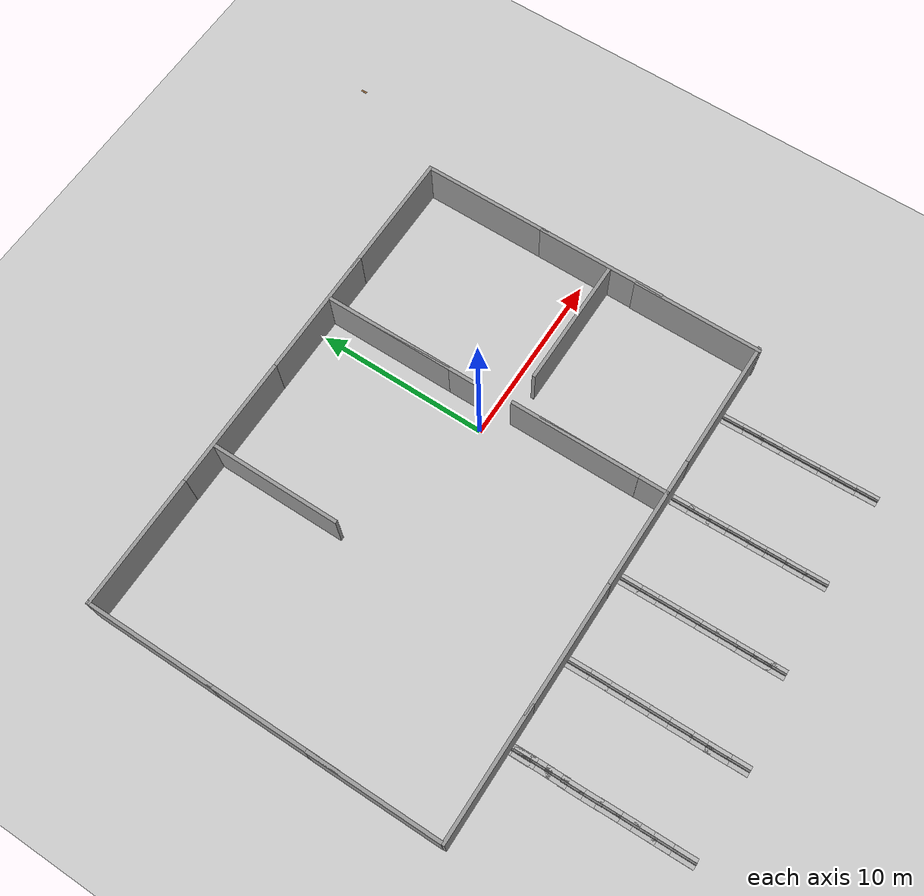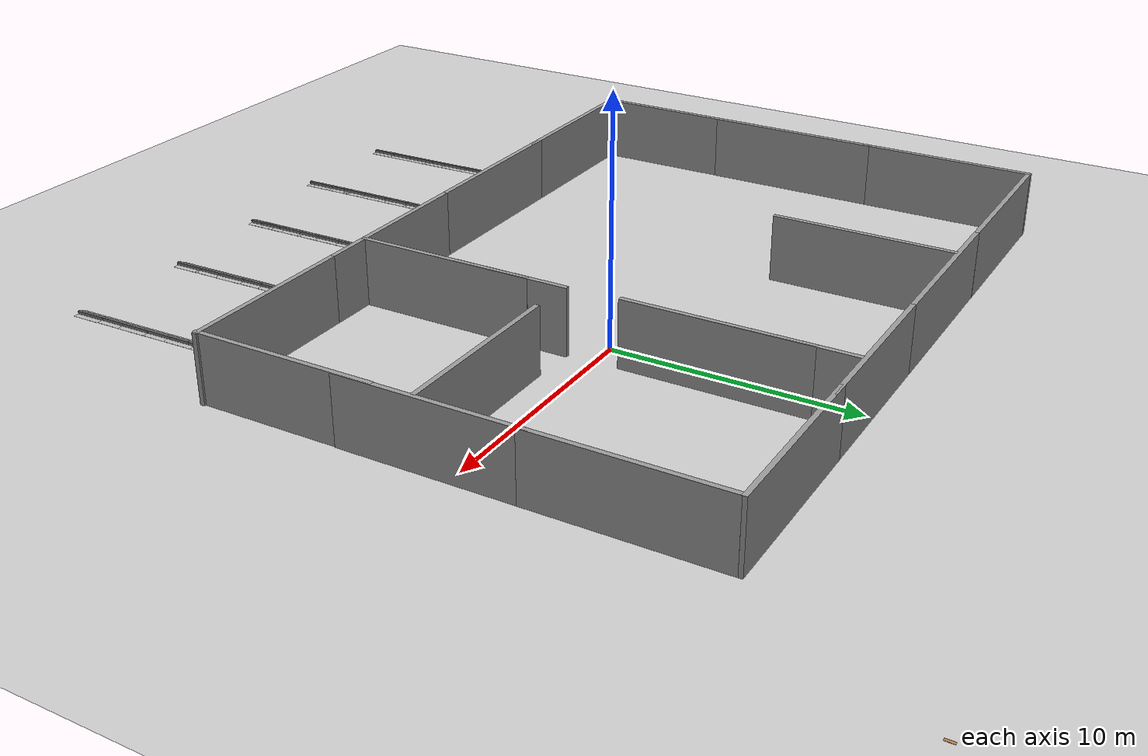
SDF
<sdf version="1.7">
 <world name="default">
  <light name="sun" type="directional">
   <pose>0 0 10 0 -0 0</pose>
   <diffuse>0.8 0.8 0.8 1</diffuse>
   <specular>0.2 0.2 0.2 1</specular>
   <attenuation>
    <range>1000</range>
    <constant>0.9</constant>
    <linear>0.01</linear>
    <quadratic>0.001</quadratic>
   </attenuation>
   <direction>-0.5 0.1 -0.9</direction>
   <spot><inner_angle>0</inner_angle><outer_angle>0</outer_angle><falloff>0</falloff></spot>
  </light>
  <model name="ground_plane">
   <static>1</static>
   <link name="link">
    <collision name="collision">
     <geometry><plane><normal>0 0 1</normal><size>100 100</size></plane></geometry>
     <surface>
      <contact><collide_bitmask>65535</collide_bitmask></contact>
      <friction><ode><mu>100</mu><mu2>50</mu2></ode></friction>
     </surface>
    </collision>
    <visual name="visual">
     <cast_shadows>0</cast_shadows>
     <geometry><plane><normal>0 0 1</normal><size>100 100</size></plane></geometry>
     <material>
      <script><uri>file://media/materials/scripts/gazebo.material</uri><name>Gazebo/Grey</name></script>
     </material>
    </visual>
   </link>
  </model>
  <gravity>0 0 -9.8</gravity>
  <magnetic_field>6e-06 2.3e-05 -4.2e-05</magnetic_field>
  <atmosphere type="adiabatic"/>
  <physics type="ode">
   <max_step_size>0.001</max_step_size>
   <real_time_factor>1</real_time_factor>
   <real_time_update_rate>1000</real_time_update_rate>
  </physics>
  <scene><ambient>0.4 0.4 0.4 1</ambient><background>0.7 0.7 0.7 1</background><shadows>1</shadows></scene>
  <spherical_coordinates>
   <surface_model>EARTH_WGS84</surface_model>
   <latitude_deg>0</latitude_deg>
   <longitude_deg>0</longitude_deg>
   <elevation>0</elevation>
   <heading_deg>0</heading_deg>
  </spherical_coordinates>
  <model name="grey_wall">
   <static>1</static>
   <link name="link">
    <pose>0 0 1.4 0 -0 0</pose>
    <collision name="collision"><geometry><box><size>7.5 0.2 2.8</size></box></geometry></collision>
    <visual name="visual">
     <cast_shadows>0</cast_shadows>
     <geometry><box><size>7.5 0.2 2.8</size></box></geometry>
     <material>
      <script>
       <uri>https://fuel.ignitionrobotics.org/1.0/openrobotics/models/grey wall/2/files/materials/scripts</uri>
       <uri>https://fuel.ignitionrobotics.org/1.0/openrobotics/models/grey wall/2/files/materials/textures</uri>
       <name>vrc/grey_wall</name>
      </script>
     </material>
    </visual>
   </link>
   <pose>0.12422 10.16 0 0 -0 0</pose>
  </model>
  <model name="grey_wall_clone">
   <static>1</static>
   <link name="link">
    <pose>0 0 1.4 0 -0 0</pose>
    <collision name="collision"><geometry><box><size>7.5 0.2 2.8</size></box></geometry></collision>
    <visual name="visual">
     <cast_shadows>0</cast_shadows>
     <geometry><box><size>7.5 0.2 2.8</size></box></geometry>
     <material>
      <script>
       <uri>https://fuel.ignitionrobotics.org/1.0/openrobotics/models/grey wall/2/files/materials/scripts</uri>
       <uri>https://fuel.ignitionrobotics.org/1.0/openrobotics/models/grey wall/2/files/materials/textures</uri>
       <name>vrc/grey_wall</name>
      </script>
     </material>
    </visual>
   </link>
   <pose>6.92563 10.1635 0 0 -0 0</pose>
  </model>
  <model name="grey_wall_clone_0">
   <static>1</static>
   <link name="link">
    <pose>0 0 1.4 0 -0 0</pose>
    <collision name="collision"><geometry><box><size>7.5 0.2 2.8</size></box></geometry></collision>
    <visual name="visual">
     <cast_shadows>0</cast_shadows>
     <geometry><box><size>7.5 0.2 2.8</size></box></geometry>
     <material>
      <script>
       <uri>https://fuel.ignitionrobotics.org/1.0/openrobotics/models/grey wall/2/files/materials/scripts</uri>
       <uri>https://fuel.ignitionrobotics.org/1.0/openrobotics/models/grey wall/2/files/materials/textures</uri>
       <name>vrc/grey_wall</name>
      </script>
     </material>
    </visual>
   </link>
   <pose>-7.35355 10.1615 0 0 -0 0</pose>
  </model>
  <model name="grey_wall_clone_1">
   <static>1</static>
   <link name="link">
    <pose>0 0 1.4 0 -0 0</pose>
    <collision name="collision"><geometry><box><size>7.5 0.2 2.8</size></box></geometry></collision>
    <visual name="visual">
     <cast_shadows>0</cast_shadows>
     <geometry><box><size>7.5 0.2 2.8</size></box></geometry>
     <material>
      <script>
       <uri>https://fuel.ignitionrobotics.org/1.0/openrobotics/models/grey wall/2/files/materials/scripts</uri>
       <uri>https://fuel.ignitionrobotics.org/1.0/openrobotics/models/grey wall/2/files/materials/textures</uri>
       <name>vrc/grey_wall</name>
      </script>
     </material>
    </visual>
   </link>
   <pose>-14.8373 10.1676 0 0 -0 0</pose>
  </model>
  <model name="grey_wall_clone_2">
   <static>1</static>
   <link name="link">
    <pose>0 0 1.4 0 -0 0</pose>
    <collision name="collision"><geometry><box><size>7.5 0.2 2.8</size></box></geometry></collision>
    <visual name="visual">
     <cast_shadows>0</cast_shadows>
     <geometry><box><size>7.5 0.2 2.8</size></box></geometry>
     <material>
      <script>
       <uri>https://fuel.ignitionrobotics.org/1.0/openrobotics/models/grey wall/2/files/materials/scripts</uri>
       <uri>https://fuel.ignitionrobotics.org/1.0/openrobotics/models/grey wall/2/files/materials/textures</uri>
       <name>vrc/grey_wall</name>
      </script>
     </material>
    </visual>
   </link>
   <pose>7.07156 -10.1705 0 0 -0 0</pose>
  </model>
  <model name="grey_wall_clone_3">
   <static>1</static>
   <link name="link">
    <pose>0 0 1.4 0 -0 0</pose>
    <collision name="collision"><geometry><box><size>7.5 0.2 2.8</size></box></geometry></collision>
    <visual name="visual">
     <cast_shadows>0</cast_shadows>
     <geometry><box><size>7.5 0.2 2.8</size></box></geometry>
     <material>
      <script>
       <uri>https://fuel.ignitionrobotics.org/1.0/openrobotics/models/grey wall/2/files/materials/scripts</uri>
       <uri>https://fuel.ignitionrobotics.org/1.0/openrobotics/models/grey wall/2/files/materials/textures</uri>
       <name>vrc/grey_wall</name>
      </script>
     </material>
    </visual>
   </link>
   <pose>-0.417375 -10.1706 0 0 -0 0</pose>
  </model>
  <model name="grey_wall_clone_4">
   <static>1</static>
   <link name="link">
    <pose>0 0 1.4 0 -0 0</pose>
    <collision name="collision"><geometry><box><size>7.5 0.2 2.8</size></box></geometry></collision>
    <visual name="visual">
     <cast_shadows>0</cast_shadows>
     <geometry><box><size>7.5 0.2 2.8</size></box></geometry>
     <material>
      <script>
       <uri>https://fuel.ignitionrobotics.org/1.0/openrobotics/models/grey wall/2/files/materials/scripts</uri>
       <uri>https://fuel.ignitionrobotics.org/1.0/openrobotics/models/grey wall/2/files/materials/textures</uri>
       <name>vrc/grey_wall</name>
      </script>
     </material>
    </visual>
   </link>
   <pose>-7.91135 -10.1718 0 0 -0 0</pose>
  </model>
  <model name="grey_wall_clone_5">
   <static>1</static>
   <link name="link">
    <pose>0 0 1.4 0 -0 0</pose>
    <collision name="collision"><geometry><box><size>7.5 0.2 2.8</size></box></geometry></collision>
    <visual name="visual">
     <cast_shadows>0</cast_shadows>
     <geometry><box><size>7.5 0.2 2.8</size></box></geometry>
     <material>
      <script>
       <uri>https://fuel.ignitionrobotics.org/1.0/openrobotics/models/grey wall/2/files/materials/scripts</uri>
       <uri>https://fuel.ignitionrobotics.org/1.0/openrobotics/models/grey wall/2/files/materials/textures</uri>
       <name>vrc/grey_wall</name>
      </script>
     </material>
    </visual>
   </link>
   <pose>-14.7388 -10.1723 0 0 -0 0</pose>
  </model>
  <model name="frc2016_rockwall">
   <static>1</static>
   <link name="link">
    <inertial>
     <mass>10</mass>
     <pose>0 0 0.08974 0 -0 0</pose>
     <inertia><ixx>0.327091</ixx><ixy>0</ixy><ixz>0</ixz><iyy>1.37417</iyy><iyz>0</iyz><izz>1.64109</izz></inertia>
    </inertial>
    <visual name="platform">
     <pose>0 0 0.06432 0 -0 0</pose>
     <geometry><box><size>1.27 0.5969 0.003175</size></box></geometry>
    </visual>
    <collision name="platform">
     <pose>0 0 0.06432 0 -0 0</pose>
     <geometry><box><size>1.27 0.5969 0.003175</size></box></geometry>
    </collision>
    <visual name="up1">
     <pose>0 0.05166 0.12537 0 -0 0</pose>
     <geometry><box><size>1.27 0.00462 0.11892</size></box></geometry>
     <material><ambient>0.46 0.46 0.46 1</ambient><diffuse>0.46 0.46 0.46 1</diffuse></material>
    </visual>
    <collision name="up1">
     <pose>0 0.05166 0.12537 0 -0 0</pose>
     <geometry><box><size>1.27 0.00462 0.11892</size></box></geometry>
    </collision>
    <visual name="up2">
     <pose>0 -0.05801 0.12537 0 -0 0</pose>
     <geometry><box><size>1.27 0.00462 0.11892</size></box></geometry>
     <material><ambient>0.46 0.46 0.46 1</ambient><diffuse>0.46 0.46 0.46 1</diffuse></material>
    </visual>
    <collision name="up2">
     <pose>0 -0.05801 0.12537 0 -0 0</pose>
     <geometry><box><size>1.27 0.00462 0.11892</size></box></geometry>
    </collision>
    <visual name="top">
     <pose>0 -0.00249 0.18252 0 -0 0</pose>
     <geometry><box><size>1.27 0.1143 0.00462</size></box></geometry>
     <material><ambient>0.46 0.46 0.46 1</ambient><diffuse>0.46 0.46 0.46 1</diffuse></material>
    </visual>
    <collision name="top">
     <pose>0 -0.00249 0.18252 0 -0 0</pose>
     <geometry><box><size>1.27 0.1143 0.00462</size></box></geometry>
    </collision>
   </link>
   <pose>7.57205 -10.9231 0 0 -0 1.59626</pose>
  </model>
  <model name="grey_wall_clone_2_clone">
   <static>1</static>
   <link name="link">
    <pose>0 0 1.4 0 -0 0</pose>
    <collision name="collision"><geometry><box><size>7.5 0.2 2.8</size></box></geometry></collision>
    <visual name="visual">
     <cast_shadows>0</cast_shadows>
     <geometry><box><size>7.5 0.2 2.8</size></box></geometry>
     <material>
      <script>
       <uri>https://fuel.ignitionrobotics.org/1.0/openrobotics/models/grey wall/2/files/materials/scripts</uri>
       <uri>https://fuel.ignitionrobotics.org/1.0/openrobotics/models/grey wall/2/files/materials/textures</uri>
       <name>vrc/grey_wall</name>
      </script>
     </material>
    </visual>
   </link>
   <pose>10.6239 -6.57923 0 0 -0 1.5756</pose>
  </model>
  <model name="grey_wall_clone_2_clone_clone">
   <static>1</static>
   <link name="link">
    <pose>0 0 1.4 0 -0 0</pose>
    <collision name="collision"><geometry><box><size>7.5 0.2 2.8</size></box></geometry></collision>
    <visual name="visual">
     <cast_shadows>0</cast_shadows>
     <geometry><box><size>7.5 0.2 2.8</size></box></geometry>
     <material>
      <script>
       <uri>https://fuel.ignitionrobotics.org/1.0/openrobotics/models/grey wall/2/files/materials/scripts</uri>
       <uri>https://fuel.ignitionrobotics.org/1.0/openrobotics/models/grey wall/2/files/materials/textures</uri>
       <name>vrc/grey_wall</name>
      </script>
     </material>
    </visual>
   </link>
   <pose>10.6274 -0.701461 0 0 -0 1.5756</pose>
  </model>
  <model name="grey_wall_clone_2_clone_clone_0">
   <static>1</static>
   <link name="link">
    <pose>0 0 1.4 0 -0 0</pose>
    <collision name="collision"><geometry><box><size>7.5 0.2 2.8</size></box></geometry></collision>
    <visual name="visual">
     <cast_shadows>0</cast_shadows>
     <geometry><box><size>7.5 0.2 2.8</size></box></geometry>
     <material>
      <script>
       <uri>https://fuel.ignitionrobotics.org/1.0/openrobotics/models/grey wall/2/files/materials/scripts</uri>
       <uri>https://fuel.ignitionrobotics.org/1.0/openrobotics/models/grey wall/2/files/materials/textures</uri>
       <name>vrc/grey_wall</name>
      </script>
     </material>
    </visual>
   </link>
   <pose>10.5981 6.34643 0 0 -0 1.5756</pose>
  </model>
  <model name="grey_wall_clone_3_clone">
   <static>1</static>
   <link name="link">
    <pose>0 0 1.4 0 -0 0</pose>
    <collision name="collision"><geometry><box><size>7.5 0.2 2.8</size></box></geometry></collision>
    <visual name="visual">
     <cast_shadows>0</cast_shadows>
     <geometry><box><size>7.5 0.2 2.8</size></box></geometry>
     <material>
      <script>
       <uri>https://fuel.ignitionrobotics.org/1.0/openrobotics/models/grey wall/2/files/materials/scripts</uri>
       <uri>https://fuel.ignitionrobotics.org/1.0/openrobotics/models/grey wall/2/files/materials/textures</uri>
       <name>vrc/grey_wall</name>
      </script>
     </material>
    </visual>
   </link>
   <pose>6.82309 -1.27324 0 0 -0 0</pose>
  </model>
  <model name="grey_wall_clone_2_clone_clone_1">
   <static>1</static>
   <link name="link">
    <pose>0 0 1.4 0 -0 0</pose>
    <collision name="collision"><geometry><box><size>7.5 0.2 2.8</size></box></geometry></collision>
    <visual name="visual">
     <cast_shadows>0</cast_shadows>
     <geometry><box><size>7.5 0.2 2.8</size></box></geometry>
     <material>
      <script>
       <uri>https://fuel.ignitionrobotics.org/1.0/openrobotics/models/grey wall/2/files/materials/scripts</uri>
       <uri>https://fuel.ignitionrobotics.org/1.0/openrobotics/models/grey wall/2/files/materials/textures</uri>
       <name>vrc/grey_wall</name>
      </script>
     </material>
    </visual>
   </link>
   <pose>1.30679 -4.83365 0 0 -0 1.5756</pose>
  </model>
  <model name="grey_wall_clone_2_clone_clone_1_clone">
   <static>1</static>
   <link name="link">
    <pose>0 0 1.4 0 -0 0</pose>
    <collision name="collision"><geometry><box><size>7.5 0.2 2.8</size></box></geometry></collision>
    <visual name="visual">
     <cast_shadows>0</cast_shadows>
     <geometry><box><size>7.5 0.2 2.8</size></box></geometry>
     <material>
      <script>
       <uri>https://fuel.ignitionrobotics.org/1.0/openrobotics/models/grey wall/2/files/materials/scripts</uri>
       <uri>https://fuel.ignitionrobotics.org/1.0/openrobotics/models/grey wall/2/files/materials/textures</uri>
       <name>vrc/grey_wall</name>
      </script>
     </material>
    </visual>
   </link>
   <pose>1.32492 -6.49418 0 0 -0 1.5756</pose>
  </model>
  <model name="frc2016_rockwall_clone">
   <static>1</static>
   <link name="link">
    <inertial>
     <mass>10</mass>
     <pose>0 0 0.08974 0 -0 0</pose>
     <inertia><ixx>0.327091</ixx><ixy>0</ixy><ixz>0</ixz><iyy>1.37417</iyy><iyz>0</iyz><izz>1.64109</izz></inertia>
    </inertial>
    <visual name="platform">
     <pose>0 0 0.06432 0 -0 0</pose>
     <geometry><box><size>1.27 0.5969 0.003175</size></box></geometry>
    </visual>
    <collision name="platform">
     <pose>0 0 0.06432 0 -0 0</pose>
     <geometry><box><size>1.27 0.5969 0.003175</size></box></geometry>
    </collision>
    <visual name="up1">
     <pose>0 0.05166 0.12537 0 -0 0</pose>
     <geometry><box><size>1.27 0.00462 0.11892</size></box></geometry>
     <material><ambient>0.46 0.46 0.46 1</ambient><diffuse>0.46 0.46 0.46 1</diffuse></material>
    </visual>
    <collision name="up1">
     <pose>0 0.05166 0.12537 0 -0 0</pose>
     <geometry><box><size>1.27 0.00462 0.11892</size></box></geometry>
    </collision>
    <visual name="up2">
     <pose>0 -0.05801 0.12537 0 -0 0</pose>
     <geometry><box><size>1.27 0.00462 0.11892</size></box></geometry>
     <material><ambient>0.46 0.46 0.46 1</ambient><diffuse>0.46 0.46 0.46 1</diffuse></material>
    </visual>
    <collision name="up2">
     <pose>0 -0.05801 0.12537 0 -0 0</pose>
     <geometry><box><size>1.27 0.00462 0.11892</size></box></geometry>
    </collision>
    <visual name="top">
     <pose>0 -0.00249 0.18252 0 -0 0</pose>
     <geometry><box><size>1.27 0.1143 0.00462</size></box></geometry>
     <material><ambient>0.46 0.46 0.46 1</ambient><diffuse>0.46 0.46 0.46 1</diffuse></material>
    </visual>
    <collision name="top">
     <pose>0 -0.00249 0.18252 0 -0 0</pose>
     <geometry><box><size>1.27 0.1143 0.00462</size></box></geometry>
    </collision>
   </link>
   <pose>7.6081 -12.0702 0 0 -0 1.59626</pose>
  </model>
  <model name="frc2016_rockwall_clone_0">
   <static>1</static>
   <link name="link">
    <inertial>
     <mass>10</mass>
     <pose>0 0 0.08974 0 -0 0</pose>
     <inertia><ixx>0.327091</ixx><ixy>0</ixy><ixz>0</ixz><iyy>1.37417</iyy><iyz>0</iyz><izz>1.64109</izz></inertia>
    </inertial>
    <visual name="platform">
     <pose>0 0 0.06432 0 -0 0</pose>
     <geometry><box><size>1.27 0.5969 0.003175</size></box></geometry>
    </visual>
    <collision name="platform">
     <pose>0 0 0.06432 0 -0 0</pose>
     <geometry><box><size>1.27 0.5969 0.003175</size></box></geometry>
    </collision>
    <visual name="up1">
     <pose>0 0.05166 0.12537 0 -0 0</pose>
     <geometry><box><size>1.27 0.00462 0.11892</size></box></geometry>
     <material><ambient>0.46 0.46 0.46 1</ambient><diffuse>0.46 0.46 0.46 1</diffuse></material>
    </visual>
    <collision name="up1">
     <pose>0 0.05166 0.12537 0 -0 0</pose>
     <geometry><box><size>1.27 0.00462 0.11892</size></box></geometry>
    </collision>
    <visual name="up2">
     <pose>0 -0.05801 0.12537 0 -0 0</pose>
     <geometry><box><size>1.27 0.00462 0.11892</size></box></geometry>
     <material><ambient>0.46 0.46 0.46 1</ambient><diffuse>0.46 0.46 0.46 1</diffuse></material>
    </visual>
    <collision name="up2">
     <pose>0 -0.05801 0.12537 0 -0 0</pose>
     <geometry><box><size>1.27 0.00462 0.11892</size></box></geometry>
    </collision>
    <visual name="top">
     <pose>0 -0.00249 0.18252 0 -0 0</pose>
     <geometry><box><size>1.27 0.1143 0.00462</size></box></geometry>
     <material><ambient>0.46 0.46 0.46 1</ambient><diffuse>0.46 0.46 0.46 1</diffuse></material>
    </visual>
    <collision name="top">
     <pose>0 -0.00249 0.18252 0 -0 0</pose>
     <geometry><box><size>1.27 0.1143 0.00462</size></box></geometry>
    </collision>
   </link>
   <pose>7.63123 -13.0973 0 0 -0 1.59626</pose>
  </model>
  <model name="frc2016_rockwall_clone_1">
   <static>1</static>
   <link name="link">
    <inertial>
     <mass>10</mass>
     <pose>0 0 0.08974 0 -0 0</pose>
     <inertia><ixx>0.327091</ixx><ixy>0</ixy><ixz>0</ixz><iyy>1.37417</iyy><iyz>0</iyz><izz>1.64109</izz></inertia>
    </inertial>
    <visual name="platform">
     <pose>0 0 0.06432 0 -0 0</pose>
     <geometry><box><size>1.27 0.5969 0.003175</size></box></geometry>
    </visual>
    <collision name="platform">
     <pose>0 0 0.06432 0 -0 0</pose>
     <geometry><box><size>1.27 0.5969 0.003175</size></box></geometry>
    </collision>
    <visual name="up1">
     <pose>0 0.05166 0.12537 0 -0 0</pose>
     <geometry><box><size>1.27 0.00462 0.11892</size></box></geometry>
     <material><ambient>0.46 0.46 0.46 1</ambient><diffuse>0.46 0.46 0.46 1</diffuse></material>
    </visual>
    <collision name="up1">
     <pose>0 0.05166 0.12537 0 -0 0</pose>
     <geometry><box><size>1.27 0.00462 0.11892</size></box></geometry>
    </collision>
    <visual name="up2">
     <pose>0 -0.05801 0.12537 0 -0 0</pose>
     <geometry><box><size>1.27 0.00462 0.11892</size></box></geometry>
     <material><ambient>0.46 0.46 0.46 1</ambient><diffuse>0.46 0.46 0.46 1</diffuse></material>
    </visual>
    <collision name="up2">
     <pose>0 -0.05801 0.12537 0 -0 0</pose>
     <geometry><box><size>1.27 0.00462 0.11892</size></box></geometry>
    </collision>
    <visual name="top">
     <pose>0 -0.00249 0.18252 0 -0 0</pose>
     <geometry><box><size>1.27 0.1143 0.00462</size></box></geometry>
     <material><ambient>0.46 0.46 0.46 1</ambient><diffuse>0.46 0.46 0.46 1</diffuse></material>
    </visual>
    <collision name="top">
     <pose>0 -0.00249 0.18252 0 -0 0</pose>
     <geometry><box><size>1.27 0.1143 0.00462</size></box></geometry>
    </collision>
   </link>
   <pose>7.65475 -14.1018 0 0 -0 1.59626</pose>
  </model>
  <model name="frc2016_rockwall_clone_2">
   <static>1</static>
   <link name="link">
    <inertial>
     <mass>10</mass>
     <pose>0 0 0.08974 0 -0 0</pose>
     <inertia><ixx>0.327091</ixx><ixy>0</ixy><ixz>0</ixz><iyy>1.37417</iyy><iyz>0</iyz><izz>1.64109</izz></inertia>
    </inertial>
    <visual name="platform">
     <pose>0 0 0.06432 0 -0 0</pose>
     <geometry><box><size>1.27 0.5969 0.003175</size></box></geometry>
    </visual>
    <collision name="platform">
     <pose>0 0 0.06432 0 -0 0</pose>
     <geometry><box><size>1.27 0.5969 0.003175</size></box></geometry>
    </collision>
    <visual name="up1">
     <pose>0 0.05166 0.12537 0 -0 0</pose>
     <geometry><box><size>1.27 0.00462 0.11892</size></box></geometry>
     <material><ambient>0.46 0.46 0.46 1</ambient><diffuse>0.46 0.46 0.46 1</diffuse></material>
    </visual>
    <collision name="up1">
     <pose>0 0.05166 0.12537 0 -0 0</pose>
     <geometry><box><size>1.27 0.00462 0.11892</size></box></geometry>
    </collision>
    <visual name="up2">
     <pose>0 -0.05801 0.12537 0 -0 0</pose>
     <geometry><box><size>1.27 0.00462 0.11892</size></box></geometry>
     <material><ambient>0.46 0.46 0.46 1</ambient><diffuse>0.46 0.46 0.46 1</diffuse></material>
    </visual>
    <collision name="up2">
     <pose>0 -0.05801 0.12537 0 -0 0</pose>
     <geometry><box><size>1.27 0.00462 0.11892</size></box></geometry>
    </collision>
    <visual name="top">
     <pose>0 -0.00249 0.18252 0 -0 0</pose>
     <geometry><box><size>1.27 0.1143 0.00462</size></box></geometry>
     <material><ambient>0.46 0.46 0.46 1</ambient><diffuse>0.46 0.46 0.46 1</diffuse></material>
    </visual>
    <collision name="top">
     <pose>0 -0.00249 0.18252 0 -0 0</pose>
     <geometry><box><size>1.27 0.1143 0.00462</size></box></geometry>
    </collision>
   </link>
   <pose>7.68671 -15.2564 0 0 -0 1.59626</pose>
  </model>
  <model name="frc2016_rockwall_clone_3">
   <static>1</static>
   <link name="link">
    <inertial>
     <mass>10</mass>
     <pose>0 0 0.08974 0 -0 0</pose>
     <inertia><ixx>0.327091</ixx><ixy>0</ixy><ixz>0</ixz><iyy>1.37417</iyy><iyz>0</iyz><izz>1.64109</izz></inertia>
    </inertial>
    <visual name="platform">
     <pose>0 0 0.06432 0 -0 0</pose>
     <geometry><box><size>1.27 0.5969 0.003175</size></box></geometry>
    </visual>
    <collision name="platform">
     <pose>0 0 0.06432 0 -0 0</pose>
     <geometry><box><size>1.27 0.5969 0.003175</size></box></geometry>
    </collision>
    <visual name="up1">
     <pose>0 0.05166 0.12537 0 -0 0</pose>
     <geometry><box><size>1.27 0.00462 0.11892</size></box></geometry>
     <material><ambient>0.46 0.46 0.46 1</ambient><diffuse>0.46 0.46 0.46 1</diffuse></material>
    </visual>
    <collision name="up1">
     <pose>0 0.05166 0.12537 0 -0 0</pose>
     <geometry><box><size>1.27 0.00462 0.11892</size></box></geometry>
    </collision>
    <visual name="up2">
     <pose>0 -0.05801 0.12537 0 -0 0</pose>
     <geometry><box><size>1.27 0.00462 0.11892</size></box></geometry>
     <material><ambient>0.46 0.46 0.46 1</ambient><diffuse>0.46 0.46 0.46 1</diffuse></material>
    </visual>
    <collision name="up2">
     <pose>0 -0.05801 0.12537 0 -0 0</pose>
     <geometry><box><size>1.27 0.00462 0.11892</size></box></geometry>
    </collision>
    <visual name="top">
     <pose>0 -0.00249 0.18252 0 -0 0</pose>
     <geometry><box><size>1.27 0.1143 0.00462</size></box></geometry>
     <material><ambient>0.46 0.46 0.46 1</ambient><diffuse>0.46 0.46 0.46 1</diffuse></material>
    </visual>
    <collision name="top">
     <pose>0 -0.00249 0.18252 0 -0 0</pose>
     <geometry><box><size>1.27 0.1143 0.00462</size></box></geometry>
    </collision>
   </link>
   <pose>7.71965 -16.3662 0 0 -0 1.59626</pose>
  </model>
  <model name="frc2016_rockwall_clone_4">
   <static>1</static>
   <link name="link">
    <inertial>
     <mass>10</mass>
     <pose>0 0 0.08974 0 -0 0</pose>
     <inertia><ixx>0.327091</ixx><ixy>0</ixy><ixz>0</ixz><iyy>1.37417</iyy><iyz>0</iyz><izz>1.64109</izz></inertia>
    </inertial>
    <visual name="platform">
     <pose>0 0 0.06432 0 -0 0</pose>
     <geometry><box><size>1.27 0.5969 0.003175</size></box></geometry>
    </visual>
    <collision name="platform">
     <pose>0 0 0.06432 0 -0 0</pose>
     <geometry><box><size>1.27 0.5969 0.003175</size></box></geometry>
    </collision>
    <visual name="up1">
     <pose>0 0.05166 0.12537 0 -0 0</pose>
     <geometry><box><size>1.27 0.00462 0.11892</size></box></geometry>
     <material><ambient>0.46 0.46 0.46 1</ambient><diffuse>0.46 0.46 0.46 1</diffuse></material>
    </visual>
    <collision name="up1">
     <pose>0 0.05166 0.12537 0 -0 0</pose>
     <geometry><box><size>1.27 0.00462 0.11892</size></box></geometry>
    </collision>
    <visual name="up2">
     <pose>0 -0.05801 0.12537 0 -0 0</pose>
     <geometry><box><size>1.27 0.00462 0.11892</size></box></geometry>
     <material><ambient>0.46 0.46 0.46 1</ambient><diffuse>0.46 0.46 0.46 1</diffuse></material>
    </visual>
    <collision name="up2">
     <pose>0 -0.05801 0.12537 0 -0 0</pose>
     <geometry><box><size>1.27 0.00462 0.11892</size></box></geometry>
    </collision>
    <visual name="top">
     <pose>0 -0.00249 0.18252 0 -0 0</pose>
     <geometry><box><size>1.27 0.1143 0.00462</size></box></geometry>
     <material><ambient>0.46 0.46 0.46 1</ambient><diffuse>0.46 0.46 0.46 1</diffuse></material>
    </visual>
    <collision name="top">
     <pose>0 -0.00249 0.18252 0 -0 0</pose>
     <geometry><box><size>1.27 0.1143 0.00462</size></box></geometry>
    </collision>
   </link>
   <pose>7.7425 -17.4078 0 0 -0 1.59626</pose>
  </model>
  <model name="frc2016_rockwall_clone_5">
   <static>1</static>
   <link name="link">
    <inertial>
     <mass>10</mass>
     <pose>0 0 0.08974 0 -0 0</pose>
     <inertia><ixx>0.327091</ixx><ixy>0</ixy><ixz>0</ixz><iyy>1.37417</iyy><iyz>0</iyz><izz>1.64109</izz></inertia>
    </inertial>
    <visual name="platform">
     <pose>0 0 0.06432 0 -0 0</pose>
     <geometry><box><size>1.27 0.5969 0.003175</size></box></geometry>
    </visual>
    <collision name="platform">
     <pose>0 0 0.06432 0 -0 0</pose>
     <geometry><box><size>1.27 0.5969 0.003175</size></box></geometry>
    </collision>
    <visual name="up1">
     <pose>0 0.05166 0.12537 0 -0 0</pose>
     <geometry><box><size>1.27 0.00462 0.11892</size></box></geometry>
     <material><ambient>0.46 0.46 0.46 1</ambient><diffuse>0.46 0.46 0.46 1</diffuse></material>
    </visual>
    <collision name="up1">
     <pose>0 0.05166 0.12537 0 -0 0</pose>
     <geometry><box><size>1.27 0.00462 0.11892</size></box></geometry>
    </collision>
    <visual name="up2">
     <pose>0 -0.05801 0.12537 0 -0 0</pose>
     <geometry><box><size>1.27 0.00462 0.11892</size></box></geometry>
     <material><ambient>0.46 0.46 0.46 1</ambient><diffuse>0.46 0.46 0.46 1</diffuse></material>
    </visual>
    <collision name="up2">
     <pose>0 -0.05801 0.12537 0 -0 0</pose>
     <geometry><box><size>1.27 0.00462 0.11892</size></box></geometry>
    </collision>
    <visual name="top">
     <pose>0 -0.00249 0.18252 0 -0 0</pose>
     <geometry><box><size>1.27 0.1143 0.00462</size></box></geometry>
     <material><ambient>0.46 0.46 0.46 1</ambient><diffuse>0.46 0.46 0.46 1</diffuse></material>
    </visual>
    <collision name="top">
     <pose>0 -0.00249 0.18252 0 -0 0</pose>
     <geometry><box><size>1.27 0.1143 0.00462</size></box></geometry>
    </collision>
   </link>
   <pose>7.78797 -18.6274 0 0 -0 1.59626</pose>
  </model>
  <model name="frc2016_rockwall_clone_6">
   <static>1</static>
   <link name="link">
    <inertial>
     <mass>10</mass>
     <pose>0 0 0.08974 0 -0 0</pose>
     <inertia><ixx>0.327091</ixx><ixy>0</ixy><ixz>0</ixz><iyy>1.37417</iyy><iyz>0</iyz><izz>1.64109</izz></inertia>
    </inertial>
    <visual name="platform">
     <pose>0 0 0.06432 0 -0 0</pose>
     <geometry><box><size>1.27 0.5969 0.003175</size></box></geometry>
    </visual>
    <collision name="platform">
     <pose>0 0 0.06432 0 -0 0</pose>
     <geometry><box><size>1.27 0.5969 0.003175</size></box></geometry>
    </collision>
    <visual name="up1">
     <pose>0 0.05166 0.12537 0 -0 0</pose>
     <geometry><box><size>1.27 0.00462 0.11892</size></box></geometry>
     <material><ambient>0.46 0.46 0.46 1</ambient><diffuse>0.46 0.46 0.46 1</diffuse></material>
    </visual>
    <collision name="up1">
     <pose>0 0.05166 0.12537 0 -0 0</pose>
     <geometry><box><size>1.27 0.00462 0.11892</size></box></geometry>
    </collision>
    <visual name="up2">
     <pose>0 -0.05801 0.12537 0 -0 0</pose>
     <geometry><box><size>1.27 0.00462 0.11892</size></box></geometry>
     <material><ambient>0.46 0.46 0.46 1</ambient><diffuse>0.46 0.46 0.46 1</diffuse></material>
    </visual>
    <collision name="up2">
     <pose>0 -0.05801 0.12537 0 -0 0</pose>
     <geometry><box><size>1.27 0.00462 0.11892</size></box></geometry>
    </collision>
    <visual name="top">
     <pose>0 -0.00249 0.18252 0 -0 0</pose>
     <geometry><box><size>1.27 0.1143 0.00462</size></box></geometry>
     <material><ambient>0.46 0.46 0.46 1</ambient><diffuse>0.46 0.46 0.46 1</diffuse></material>
    </visual>
    <collision name="top">
     <pose>0 -0.00249 0.18252 0 -0 0</pose>
     <geometry><box><size>1.27 0.1143 0.00462</size></box></geometry>
    </collision>
   </link>
   <pose>2.20397 -10.9427 0 0 -0 1.59626</pose>
  </model>
  <model name="frc2016_rockwall_clone_7">
   <static>1</static>
   <link name="link">
    <inertial>
     <mass>10</mass>
     <pose>0 0 0.08974 0 -0 0</pose>
     <inertia><ixx>0.327091</ixx><ixy>0</ixy><ixz>0</ixz><iyy>1.37417</iyy><iyz>0</iyz><izz>1.64109</izz></inertia>
    </inertial>
    <visual name="platform">
     <pose>0 0 0.06432 0 -0 0</pose>
     <geometry><box><size>1.27 0.5969 0.003175</size></box></geometry>
    </visual>
    <collision name="platform">
     <pose>0 0 0.06432 0 -0 0</pose>
     <geometry><box><size>1.27 0.5969 0.003175</size></box></geometry>
    </collision>
    <visual name="up1">
     <pose>0 0.05166 0.12537 0 -0 0</pose>
     <geometry><box><size>1.27 0.00462 0.11892</size></box></geometry>
     <material><ambient>0.46 0.46 0.46 1</ambient><diffuse>0.46 0.46 0.46 1</diffuse></material>
    </visual>
    <collision name="up1">
     <pose>0 0.05166 0.12537 0 -0 0</pose>
     <geometry><box><size>1.27 0.00462 0.11892</size></box></geometry>
    </collision>
    <visual name="up2">
     <pose>0 -0.05801 0.12537 0 -0 0</pose>
     <geometry><box><size>1.27 0.00462 0.11892</size></box></geometry>
     <material><ambient>0.46 0.46 0.46 1</ambient><diffuse>0.46 0.46 0.46 1</diffuse></material>
    </visual>
    <collision name="up2">
     <pose>0 -0.05801 0.12537 0 -0 0</pose>
     <geometry><box><size>1.27 0.00462 0.11892</size></box></geometry>
    </collision>
    <visual name="top">
     <pose>0 -0.00249 0.18252 0 -0 0</pose>
     <geometry><box><size>1.27 0.1143 0.00462</size></box></geometry>
     <material><ambient>0.46 0.46 0.46 1</ambient><diffuse>0.46 0.46 0.46 1</diffuse></material>
    </visual>
    <collision name="top">
     <pose>0 -0.00249 0.18252 0 -0 0</pose>
     <geometry><box><size>1.27 0.1143 0.00462</size></box></geometry>
    </collision>
   </link>
   <pose>2.21983 -11.9351 0 0 -0 1.59626</pose>
  </model>
  <model name="frc2016_rockwall_clone_8">
   <static>1</static>
   <link name="link">
    <inertial>
     <mass>10</mass>
     <pose>0 0 0.08974 0 -0 0</pose>
     <inertia><ixx>0.327091</ixx><ixy>0</ixy><ixz>0</ixz><iyy>1.37417</iyy><iyz>0</iyz><izz>1.64109</izz></inertia>
    </inertial>
    <visual name="platform">
     <pose>0 0 0.06432 0 -0 0</pose>
     <geometry><box><size>1.27 0.5969 0.003175</size></box></geometry>
    </visual>
    <collision name="platform">
     <pose>0 0 0.06432 0 -0 0</pose>
     <geometry><box><size>1.27 0.5969 0.003175</size></box></geometry>
    </collision>
    <visual name="up1">
     <pose>0 0.05166 0.12537 0 -0 0</pose>
     <geometry><box><size>1.27 0.00462 0.11892</size></box></geometry>
     <material><ambient>0.46 0.46 0.46 1</ambient><diffuse>0.46 0.46 0.46 1</diffuse></material>
    </visual>
    <collision name="up1">
     <pose>0 0.05166 0.12537 0 -0 0</pose>
     <geometry><box><size>1.27 0.00462 0.11892</size></box></geometry>
    </collision>
    <visual name="up2">
     <pose>0 -0.05801 0.12537 0 -0 0</pose>
     <geometry><box><size>1.27 0.00462 0.11892</size></box></geometry>
     <material><ambient>0.46 0.46 0.46 1</ambient><diffuse>0.46 0.46 0.46 1</diffuse></material>
    </visual>
    <collision name="up2">
     <pose>0 -0.05801 0.12537 0 -0 0</pose>
     <geometry><box><size>1.27 0.00462 0.11892</size></box></geometry>
    </collision>
    <visual name="top">
     <pose>0 -0.00249 0.18252 0 -0 0</pose>
     <geometry><box><size>1.27 0.1143 0.00462</size></box></geometry>
     <material><ambient>0.46 0.46 0.46 1</ambient><diffuse>0.46 0.46 0.46 1</diffuse></material>
    </visual>
    <collision name="top">
     <pose>0 -0.00249 0.18252 0 -0 0</pose>
     <geometry><box><size>1.27 0.1143 0.00462</size></box></geometry>
    </collision>
   </link>
   <pose>2.25442 -13.0397 0 0 -0 1.59626</pose>
  </model>
  <model name="frc2016_rockwall_clone_9">
   <static>1</static>
   <link name="link">
    <inertial>
     <mass>10</mass>
     <pose>0 0 0.08974 0 -0 0</pose>
     <inertia><ixx>0.327091</ixx><ixy>0</ixy><ixz>0</ixz><iyy>1.37417</iyy><iyz>0</iyz><izz>1.64109</izz></inertia>
    </inertial>
    <visual name="platform">
     <pose>0 0 0.06432 0 -0 0</pose>
     <geometry><box><size>1.27 0.5969 0.003175</size></box></geometry>
    </visual>
    <collision name="platform">
     <pose>0 0 0.06432 0 -0 0</pose>
     <geometry><box><size>1.27 0.5969 0.003175</size></box></geometry>
    </collision>
    <visual name="up1">
     <pose>0 0.05166 0.12537 0 -0 0</pose>
     <geometry><box><size>1.27 0.00462 0.11892</size></box></geometry>
     <material><ambient>0.46 0.46 0.46 1</ambient><diffuse>0.46 0.46 0.46 1</diffuse></material>
    </visual>
    <collision name="up1">
     <pose>0 0.05166 0.12537 0 -0 0</pose>
     <geometry><box><size>1.27 0.00462 0.11892</size></box></geometry>
    </collision>
    <visual name="up2">
     <pose>0 -0.05801 0.12537 0 -0 0</pose>
     <geometry><box><size>1.27 0.00462 0.11892</size></box></geometry>
     <material><ambient>0.46 0.46 0.46 1</ambient><diffuse>0.46 0.46 0.46 1</diffuse></material>
    </visual>
    <collision name="up2">
     <pose>0 -0.05801 0.12537 0 -0 0</pose>
     <geometry><box><size>1.27 0.00462 0.11892</size></box></geometry>
    </collision>
    <visual name="top">
     <pose>0 -0.00249 0.18252 0 -0 0</pose>
     <geometry><box><size>1.27 0.1143 0.00462</size></box></geometry>
     <material><ambient>0.46 0.46 0.46 1</ambient><diffuse>0.46 0.46 0.46 1</diffuse></material>
    </visual>
    <collision name="top">
     <pose>0 -0.00249 0.18252 0 -0 0</pose>
     <geometry><box><size>1.27 0.1143 0.00462</size></box></geometry>
    </collision>
   </link>
   <pose>2.28903 -14.1449 0 0 -0 1.59626</pose>
  </model>
  <model name="frc2016_rockwall_clone_10">
   <static>1</static>
   <link name="link">
    <inertial>
     <mass>10</mass>
     <pose>0 0 0.08974 0 -0 0</pose>
     <inertia><ixx>0.327091</ixx><ixy>0</ixy><ixz>0</ixz><iyy>1.37417</iyy><iyz>0</iyz><izz>1.64109</izz></inertia>
    </inertial>
    <visual name="platform">
     <pose>0 0 0.06432 0 -0 0</pose>
     <geometry><box><size>1.27 0.5969 0.003175</size></box></geometry>
    </visual>
    <collision name="platform">
     <pose>0 0 0.06432 0 -0 0</pose>
     <geometry><box><size>1.27 0.5969 0.003175</size></box></geometry>
    </collision>
    <visual name="up1">
     <pose>0 0.05166 0.12537 0 -0 0</pose>
     <geometry><box><size>1.27 0.00462 0.11892</size></box></geometry>
     <material><ambient>0.46 0.46 0.46 1</ambient><diffuse>0.46 0.46 0.46 1</diffuse></material>
    </visual>
    <collision name="up1">
     <pose>0 0.05166 0.12537 0 -0 0</pose>
     <geometry><box><size>1.27 0.00462 0.11892</size></box></geometry>
    </collision>
    <visual name="up2">
     <pose>0 -0.05801 0.12537 0 -0 0</pose>
     <geometry><box><size>1.27 0.00462 0.11892</size></box></geometry>
     <material><ambient>0.46 0.46 0.46 1</ambient><diffuse>0.46 0.46 0.46 1</diffuse></material>
    </visual>
    <collision name="up2">
     <pose>0 -0.05801 0.12537 0 -0 0</pose>
     <geometry><box><size>1.27 0.00462 0.11892</size></box></geometry>
    </collision>
    <visual name="top">
     <pose>0 -0.00249 0.18252 0 -0 0</pose>
     <geometry><box><size>1.27 0.1143 0.00462</size></box></geometry>
     <material><ambient>0.46 0.46 0.46 1</ambient><diffuse>0.46 0.46 0.46 1</diffuse></material>
    </visual>
    <collision name="top">
     <pose>0 -0.00249 0.18252 0 -0 0</pose>
     <geometry><box><size>1.27 0.1143 0.00462</size></box></geometry>
    </collision>
   </link>
   <pose>2.30895 -15.2348 0 0 -0 1.59626</pose>
  </model>
  <model name="frc2016_rockwall_clone_11">
   <static>1</static>
   <link name="link">
    <inertial>
     <mass>10</mass>
     <pose>0 0 0.08974 0 -0 0</pose>
     <inertia><ixx>0.327091</ixx><ixy>0</ixy><ixz>0</ixz><iyy>1.37417</iyy><iyz>0</iyz><izz>1.64109</izz></inertia>
    </inertial>
    <visual name="platform">
     <pose>0 0 0.06432 0 -0 0</pose>
     <geometry><box><size>1.27 0.5969 0.003175</size></box></geometry>
    </visual>
    <collision name="platform">
     <pose>0 0 0.06432 0 -0 0</pose>
     <geometry><box><size>1.27 0.5969 0.003175</size></box></geometry>
    </collision>
    <visual name="up1">
     <pose>0 0.05166 0.12537 0 -0 0</pose>
     <geometry><box><size>1.27 0.00462 0.11892</size></box></geometry>
     <material><ambient>0.46 0.46 0.46 1</ambient><diffuse>0.46 0.46 0.46 1</diffuse></material>
    </visual>
    <collision name="up1">
     <pose>0 0.05166 0.12537 0 -0 0</pose>
     <geometry><box><size>1.27 0.00462 0.11892</size></box></geometry>
    </collision>
    <visual name="up2">
     <pose>0 -0.05801 0.12537 0 -0 0</pose>
     <geometry><box><size>1.27 0.00462 0.11892</size></box></geometry>
     <material><ambient>0.46 0.46 0.46 1</ambient><diffuse>0.46 0.46 0.46 1</diffuse></material>
    </visual>
    <collision name="up2">
     <pose>0 -0.05801 0.12537 0 -0 0</pose>
     <geometry><box><size>1.27 0.00462 0.11892</size></box></geometry>
    </collision>
    <visual name="top">
     <pose>0 -0.00249 0.18252 0 -0 0</pose>
     <geometry><box><size>1.27 0.1143 0.00462</size></box></geometry>
     <material><ambient>0.46 0.46 0.46 1</ambient><diffuse>0.46 0.46 0.46 1</diffuse></material>
    </visual>
    <collision name="top">
     <pose>0 -0.00249 0.18252 0 -0 0</pose>
     <geometry><box><size>1.27 0.1143 0.00462</size></box></geometry>
    </collision>
   </link>
   <pose>2.3436 -16.3416 0 0 -0 1.59626</pose>
  </model>
  <model name="frc2016_rockwall_clone_12">
   <static>1</static>
   <link name="link">
    <inertial>
     <mass>10</mass>
     <pose>0 0 0.08974 0 -0 0</pose>
     <inertia><ixx>0.327091</ixx><ixy>0</ixy><ixz>0</ixz><iyy>1.37417</iyy><iyz>0</iyz><izz>1.64109</izz></inertia>
    </inertial>
    <visual name="platform">
     <pose>0 0 0.06432 0 -0 0</pose>
     <geometry><box><size>1.27 0.5969 0.003175</size></box></geometry>
    </visual>
    <collision name="platform">
     <pose>0 0 0.06432 0 -0 0</pose>
     <geometry><box><size>1.27 0.5969 0.003175</size></box></geometry>
    </collision>
    <visual name="up1">
     <pose>0 0.05166 0.12537 0 -0 0</pose>
     <geometry><box><size>1.27 0.00462 0.11892</size></box></geometry>
     <material><ambient>0.46 0.46 0.46 1</ambient><diffuse>0.46 0.46 0.46 1</diffuse></material>
    </visual>
    <collision name="up1">
     <pose>0 0.05166 0.12537 0 -0 0</pose>
     <geometry><box><size>1.27 0.00462 0.11892</size></box></geometry>
    </collision>
    <visual name="up2">
     <pose>0 -0.05801 0.12537 0 -0 0</pose>
     <geometry><box><size>1.27 0.00462 0.11892</size></box></geometry>
     <material><ambient>0.46 0.46 0.46 1</ambient><diffuse>0.46 0.46 0.46 1</diffuse></material>
    </visual>
    <collision name="up2">
     <pose>0 -0.05801 0.12537 0 -0 0</pose>
     <geometry><box><size>1.27 0.00462 0.11892</size></box></geometry>
    </collision>
    <visual name="top">
     <pose>0 -0.00249 0.18252 0 -0 0</pose>
     <geometry><box><size>1.27 0.1143 0.00462</size></box></geometry>
     <material><ambient>0.46 0.46 0.46 1</ambient><diffuse>0.46 0.46 0.46 1</diffuse></material>
    </visual>
    <collision name="top">
     <pose>0 -0.00249 0.18252 0 -0 0</pose>
     <geometry><box><size>1.27 0.1143 0.00462</size></box></geometry>
    </collision>
   </link>
   <pose>2.36356 -17.4332 0 0 -0 1.59626</pose>
  </model>
  <model name="frc2016_rockwall_clone_13">
   <static>1</static>
   <link name="link">
    <inertial>
     <mass>10</mass>
     <pose>0 0 0.08974 0 -0 0</pose>
     <inertia><ixx>0.327091</ixx><ixy>0</ixy><ixz>0</ixz><iyy>1.37417</iyy><iyz>0</iyz><izz>1.64109</izz></inertia>
    </inertial>
    <visual name="platform">
     <pose>0 0 0.06432 0 -0 0</pose>
     <geometry><box><size>1.27 0.5969 0.003175</size></box></geometry>
    </visual>
    <collision name="platform">
     <pose>0 0 0.06432 0 -0 0</pose>
     <geometry><box><size>1.27 0.5969 0.003175</size></box></geometry>
    </collision>
    <visual name="up1">
     <pose>0 0.05166 0.12537 0 -0 0</pose>
     <geometry><box><size>1.27 0.00462 0.11892</size></box></geometry>
     <material><ambient>0.46 0.46 0.46 1</ambient><diffuse>0.46 0.46 0.46 1</diffuse></material>
    </visual>
    <collision name="up1">
     <pose>0 0.05166 0.12537 0 -0 0</pose>
     <geometry><box><size>1.27 0.00462 0.11892</size></box></geometry>
    </collision>
    <visual name="up2">
     <pose>0 -0.05801 0.12537 0 -0 0</pose>
     <geometry><box><size>1.27 0.00462 0.11892</size></box></geometry>
     <material><ambient>0.46 0.46 0.46 1</ambient><diffuse>0.46 0.46 0.46 1</diffuse></material>
    </visual>
    <collision name="up2">
     <pose>0 -0.05801 0.12537 0 -0 0</pose>
     <geometry><box><size>1.27 0.00462 0.11892</size></box></geometry>
    </collision>
    <visual name="top">
     <pose>0 -0.00249 0.18252 0 -0 0</pose>
     <geometry><box><size>1.27 0.1143 0.00462</size></box></geometry>
     <material><ambient>0.46 0.46 0.46 1</ambient><diffuse>0.46 0.46 0.46 1</diffuse></material>
    </visual>
    <collision name="top">
     <pose>0 -0.00249 0.18252 0 -0 0</pose>
     <geometry><box><size>1.27 0.1143 0.00462</size></box></geometry>
    </collision>
   </link>
   <pose>2.39785 -18.5562 0 0 -0 1.59626</pose>
  </model>
  <model name="frc2016_rockwall_clone_14">
   <static>1</static>
   <link name="link">
    <inertial>
     <mass>10</mass>
     <pose>0 0 0.08974 0 -0 0</pose>
     <inertia><ixx>0.327091</ixx><ixy>0</ixy><ixz>0</ixz><iyy>1.37417</iyy><iyz>0</iyz><izz>1.64109</izz></inertia>
    </inertial>
    <visual name="platform">
     <pose>0 0 0.06432 0 -0 0</pose>
     <geometry><box><size>1.27 0.5969 0.003175</size></box></geometry>
    </visual>
    <collision name="platform">
     <pose>0 0 0.06432 0 -0 0</pose>
     <geometry><box><size>1.27 0.5969 0.003175</size></box></geometry>
    </collision>
    <visual name="up1">
     <pose>0 0.05166 0.12537 0 -0 0</pose>
     <geometry><box><size>1.27 0.00462 0.11892</size></box></geometry>
     <material><ambient>0.46 0.46 0.46 1</ambient><diffuse>0.46 0.46 0.46 1</diffuse></material>
    </visual>
    <collision name="up1">
     <pose>0 0.05166 0.12537 0 -0 0</pose>
     <geometry><box><size>1.27 0.00462 0.11892</size></box></geometry>
    </collision>
    <visual name="up2">
     <pose>0 -0.05801 0.12537 0 -0 0</pose>
     <geometry><box><size>1.27 0.00462 0.11892</size></box></geometry>
     <material><ambient>0.46 0.46 0.46 1</ambient><diffuse>0.46 0.46 0.46 1</diffuse></material>
    </visual>
    <collision name="up2">
     <pose>0 -0.05801 0.12537 0 -0 0</pose>
     <geometry><box><size>1.27 0.00462 0.11892</size></box></geometry>
    </collision>
    <visual name="top">
     <pose>0 -0.00249 0.18252 0 -0 0</pose>
     <geometry><box><size>1.27 0.1143 0.00462</size></box></geometry>
     <material><ambient>0.46 0.46 0.46 1</ambient><diffuse>0.46 0.46 0.46 1</diffuse></material>
    </visual>
    <collision name="top">
     <pose>0 -0.00249 0.18252 0 -0 0</pose>
     <geometry><box><size>1.27 0.1143 0.00462</size></box></geometry>
    </collision>
   </link>
   <pose>-2.84765 -10.8009 0 0 -0 1.59626</pose>
  </model>
  <model name="frc2016_rockwall_clone_15">
   <static>1</static>
   <link name="link">
    <inertial>
     <mass>10</mass>
     <pose>0 0 0.08974 0 -0 0</pose>
     <inertia><ixx>0.327091</ixx><ixy>0</ixy><ixz>0</ixz><iyy>1.37417</iyy><iyz>0</iyz><izz>1.64109</izz></inertia>
    </inertial>
    <visual name="platform">
     <pose>0 0 0.06432 0 -0 0</pose>
     <geometry><box><size>1.27 0.5969 0.003175</size></box></geometry>
    </visual>
    <collision name="platform">
     <pose>0 0 0.06432 0 -0 0</pose>
     <geometry><box><size>1.27 0.5969 0.003175</size></box></geometry>
    </collision>
    <visual name="up1">
     <pose>0 0.05166 0.12537 0 -0 0</pose>
     <geometry><box><size>1.27 0.00462 0.11892</size></box></geometry>
     <material><ambient>0.46 0.46 0.46 1</ambient><diffuse>0.46 0.46 0.46 1</diffuse></material>
    </visual>
    <collision name="up1">
     <pose>0 0.05166 0.12537 0 -0 0</pose>
     <geometry><box><size>1.27 0.00462 0.11892</size></box></geometry>
    </collision>
    <visual name="up2">
     <pose>0 -0.05801 0.12537 0 -0 0</pose>
     <geometry><box><size>1.27 0.00462 0.11892</size></box></geometry>
     <material><ambient>0.46 0.46 0.46 1</ambient><diffuse>0.46 0.46 0.46 1</diffuse></material>
    </visual>
    <collision name="up2">
     <pose>0 -0.05801 0.12537 0 -0 0</pose>
     <geometry><box><size>1.27 0.00462 0.11892</size></box></geometry>
    </collision>
    <visual name="top">
     <pose>0 -0.00249 0.18252 0 -0 0</pose>
     <geometry><box><size>1.27 0.1143 0.00462</size></box></geometry>
     <material><ambient>0.46 0.46 0.46 1</ambient><diffuse>0.46 0.46 0.46 1</diffuse></material>
    </visual>
    <collision name="top">
     <pose>0 -0.00249 0.18252 0 -0 0</pose>
     <geometry><box><size>1.27 0.1143 0.00462</size></box></geometry>
    </collision>
   </link>
   <pose>-2.81842 -11.9541 0 0 -0 1.59626</pose>
  </model>
  <model name="frc2016_rockwall_clone_16">
   <static>1</static>
   <link name="link">
    <inertial>
     <mass>10</mass>
     <pose>0 0 0.08974 0 -0 0</pose>
     <inertia><ixx>0.327091</ixx><ixy>0</ixy><ixz>0</ixz><iyy>1.37417</iyy><iyz>0</iyz><izz>1.64109</izz></inertia>
    </inertial>
    <visual name="platform">
     <pose>0 0 0.06432 0 -0 0</pose>
     <geometry><box><size>1.27 0.5969 0.003175</size></box></geometry>
    </visual>
    <collision name="platform">
     <pose>0 0 0.06432 0 -0 0</pose>
     <geometry><box><size>1.27 0.5969 0.003175</size></box></geometry>
    </collision>
    <visual name="up1">
     <pose>0 0.05166 0.12537 0 -0 0</pose>
     <geometry><box><size>1.27 0.00462 0.11892</size></box></geometry>
     <material><ambient>0.46 0.46 0.46 1</ambient><diffuse>0.46 0.46 0.46 1</diffuse></material>
    </visual>
    <collision name="up1">
     <pose>0 0.05166 0.12537 0 -0 0</pose>
     <geometry><box><size>1.27 0.00462 0.11892</size></box></geometry>
    </collision>
    <visual name="up2">
     <pose>0 -0.05801 0.12537 0 -0 0</pose>
     <geometry><box><size>1.27 0.00462 0.11892</size></box></geometry>
     <material><ambient>0.46 0.46 0.46 1</ambient><diffuse>0.46 0.46 0.46 1</diffuse></material>
    </visual>
    <collision name="up2">
     <pose>0 -0.05801 0.12537 0 -0 0</pose>
     <geometry><box><size>1.27 0.00462 0.11892</size></box></geometry>
    </collision>
    <visual name="top">
     <pose>0 -0.00249 0.18252 0 -0 0</pose>
     <geometry><box><size>1.27 0.1143 0.00462</size></box></geometry>
     <material><ambient>0.46 0.46 0.46 1</ambient><diffuse>0.46 0.46 0.46 1</diffuse></material>
    </visual>
    <collision name="top">
     <pose>0 -0.00249 0.18252 0 -0 0</pose>
     <geometry><box><size>1.27 0.1143 0.00462</size></box></geometry>
    </collision>
   </link>
   <pose>-2.78684 -13.0226 0 0 -0 1.59626</pose>
  </model>
  <model name="frc2016_rockwall_clone_17">
   <static>1</static>
   <link name="link">
    <inertial>
     <mass>10</mass>
     <pose>0 0 0.08974 0 -0 0</pose>
     <inertia><ixx>0.327091</ixx><ixy>0</ixy><ixz>0</ixz><iyy>1.37417</iyy><iyz>0</iyz><izz>1.64109</izz></inertia>
    </inertial>
    <visual name="platform">
     <pose>0 0 0.06432 0 -0 0</pose>
     <geometry><box><size>1.27 0.5969 0.003175</size></box></geometry>
    </visual>
    <collision name="platform">
     <pose>0 0 0.06432 0 -0 0</pose>
     <geometry><box><size>1.27 0.5969 0.003175</size></box></geometry>
    </collision>
    <visual name="up1">
     <pose>0 0.05166 0.12537 0 -0 0</pose>
     <geometry><box><size>1.27 0.00462 0.11892</size></box></geometry>
     <material><ambient>0.46 0.46 0.46 1</ambient><diffuse>0.46 0.46 0.46 1</diffuse></material>
    </visual>
    <collision name="up1">
     <pose>0 0.05166 0.12537 0 -0 0</pose>
     <geometry><box><size>1.27 0.00462 0.11892</size></box></geometry>
    </collision>
    <visual name="up2">
     <pose>0 -0.05801 0.12537 0 -0 0</pose>
     <geometry><box><size>1.27 0.00462 0.11892</size></box></geometry>
     <material><ambient>0.46 0.46 0.46 1</ambient><diffuse>0.46 0.46 0.46 1</diffuse></material>
    </visual>
    <collision name="up2">
     <pose>0 -0.05801 0.12537 0 -0 0</pose>
     <geometry><box><size>1.27 0.00462 0.11892</size></box></geometry>
    </collision>
    <visual name="top">
     <pose>0 -0.00249 0.18252 0 -0 0</pose>
     <geometry><box><size>1.27 0.1143 0.00462</size></box></geometry>
     <material><ambient>0.46 0.46 0.46 1</ambient><diffuse>0.46 0.46 0.46 1</diffuse></material>
    </visual>
    <collision name="top">
     <pose>0 -0.00249 0.18252 0 -0 0</pose>
     <geometry><box><size>1.27 0.1143 0.00462</size></box></geometry>
    </collision>
   </link>
   <pose>-2.75795 -14.2058 0 0 -0 1.59626</pose>
  </model>
  <model name="frc2016_rockwall_clone_18">
   <static>1</static>
   <link name="link">
    <inertial>
     <mass>10</mass>
     <pose>0 0 0.08974 0 -0 0</pose>
     <inertia><ixx>0.327091</ixx><ixy>0</ixy><ixz>0</ixz><iyy>1.37417</iyy><iyz>0</iyz><izz>1.64109</izz></inertia>
    </inertial>
    <visual name="platform">
     <pose>0 0 0.06432 0 -0 0</pose>
     <geometry><box><size>1.27 0.5969 0.003175</size></box></geometry>
    </visual>
    <collision name="platform">
     <pose>0 0 0.06432 0 -0 0</pose>
     <geometry><box><size>1.27 0.5969 0.003175</size></box></geometry>
    </collision>
    <visual name="up1">
     <pose>0 0.05166 0.12537 0 -0 0</pose>
     <geometry><box><size>1.27 0.00462 0.11892</size></box></geometry>
     <material><ambient>0.46 0.46 0.46 1</ambient><diffuse>0.46 0.46 0.46 1</diffuse></material>
    </visual>
    <collision name="up1">
     <pose>0 0.05166 0.12537 0 -0 0</pose>
     <geometry><box><size>1.27 0.00462 0.11892</size></box></geometry>
    </collision>
    <visual name="up2">
     <pose>0 -0.05801 0.12537 0 -0 0</pose>
     <geometry><box><size>1.27 0.00462 0.11892</size></box></geometry>
     <material><ambient>0.46 0.46 0.46 1</ambient><diffuse>0.46 0.46 0.46 1</diffuse></material>
    </visual>
    <collision name="up2">
     <pose>0 -0.05801 0.12537 0 -0 0</pose>
     <geometry><box><size>1.27 0.00462 0.11892</size></box></geometry>
    </collision>
    <visual name="top">
     <pose>0 -0.00249 0.18252 0 -0 0</pose>
     <geometry><box><size>1.27 0.1143 0.00462</size></box></geometry>
     <material><ambient>0.46 0.46 0.46 1</ambient><diffuse>0.46 0.46 0.46 1</diffuse></material>
    </visual>
    <collision name="top">
     <pose>0 -0.00249 0.18252 0 -0 0</pose>
     <geometry><box><size>1.27 0.1143 0.00462</size></box></geometry>
    </collision>
   </link>
   <pose>-2.73758 -15.2758 0 0 -0 1.59626</pose>
  </model>
  <model name="frc2016_rockwall_clone_19">
   <static>1</static>
   <link name="link">
    <inertial>
     <mass>10</mass>
     <pose>0 0 0.08974 0 -0 0</pose>
     <inertia><ixx>0.327091</ixx><ixy>0</ixy><ixz>0</ixz><iyy>1.37417</iyy><iyz>0</iyz><izz>1.64109</izz></inertia>
    </inertial>
    <visual name="platform">
     <pose>0 0 0.06432 0 -0 0</pose>
     <geometry><box><size>1.27 0.5969 0.003175</size></box></geometry>
    </visual>
    <collision name="platform">
     <pose>0 0 0.06432 0 -0 0</pose>
     <geometry><box><size>1.27 0.5969 0.003175</size></box></geometry>
    </collision>
    <visual name="up1">
     <pose>0 0.05166 0.12537 0 -0 0</pose>
     <geometry><box><size>1.27 0.00462 0.11892</size></box></geometry>
     <material><ambient>0.46 0.46 0.46 1</ambient><diffuse>0.46 0.46 0.46 1</diffuse></material>
    </visual>
    <collision name="up1">
     <pose>0 0.05166 0.12537 0 -0 0</pose>
     <geometry><box><size>1.27 0.00462 0.11892</size></box></geometry>
    </collision>
    <visual name="up2">
     <pose>0 -0.05801 0.12537 0 -0 0</pose>
     <geometry><box><size>1.27 0.00462 0.11892</size></box></geometry>
     <material><ambient>0.46 0.46 0.46 1</ambient><diffuse>0.46 0.46 0.46 1</diffuse></material>
    </visual>
    <collision name="up2">
     <pose>0 -0.05801 0.12537 0 -0 0</pose>
     <geometry><box><size>1.27 0.00462 0.11892</size></box></geometry>
    </collision>
    <visual name="top">
     <pose>0 -0.00249 0.18252 0 -0 0</pose>
     <geometry><box><size>1.27 0.1143 0.00462</size></box></geometry>
     <material><ambient>0.46 0.46 0.46 1</ambient><diffuse>0.46 0.46 0.46 1</diffuse></material>
    </visual>
    <collision name="top">
     <pose>0 -0.00249 0.18252 0 -0 0</pose>
     <geometry><box><size>1.27 0.1143 0.00462</size></box></geometry>
    </collision>
   </link>
   <pose>-2.71544 -16.2668 0 0 -0 1.59626</pose>
  </model>
  <model name="frc2016_rockwall_clone_20">
   <static>1</static>
   <link name="link">
    <inertial>
     <mass>10</mass>
     <pose>0 0 0.08974 0 -0 0</pose>
     <inertia><ixx>0.327091</ixx><ixy>0</ixy><ixz>0</ixz><iyy>1.37417</iyy><iyz>0</iyz><izz>1.64109</izz></inertia>
    </inertial>
    <visual name="platform">
     <pose>0 0 0.06432 0 -0 0</pose>
     <geometry><box><size>1.27 0.5969 0.003175</size></box></geometry>
    </visual>
    <collision name="platform">
     <pose>0 0 0.06432 0 -0 0</pose>
     <geometry><box><size>1.27 0.5969 0.003175</size></box></geometry>
    </collision>
    <visual name="up1">
     <pose>0 0.05166 0.12537 0 -0 0</pose>
     <geometry><box><size>1.27 0.00462 0.11892</size></box></geometry>
     <material><ambient>0.46 0.46 0.46 1</ambient><diffuse>0.46 0.46 0.46 1</diffuse></material>
    </visual>
    <collision name="up1">
     <pose>0 0.05166 0.12537 0 -0 0</pose>
     <geometry><box><size>1.27 0.00462 0.11892</size></box></geometry>
    </collision>
    <visual name="up2">
     <pose>0 -0.05801 0.12537 0 -0 0</pose>
     <geometry><box><size>1.27 0.00462 0.11892</size></box></geometry>
     <material><ambient>0.46 0.46 0.46 1</ambient><diffuse>0.46 0.46 0.46 1</diffuse></material>
    </visual>
    <collision name="up2">
     <pose>0 -0.05801 0.12537 0 -0 0</pose>
     <geometry><box><size>1.27 0.00462 0.11892</size></box></geometry>
    </collision>
    <visual name="top">
     <pose>0 -0.00249 0.18252 0 -0 0</pose>
     <geometry><box><size>1.27 0.1143 0.00462</size></box></geometry>
     <material><ambient>0.46 0.46 0.46 1</ambient><diffuse>0.46 0.46 0.46 1</diffuse></material>
    </visual>
    <collision name="top">
     <pose>0 -0.00249 0.18252 0 -0 0</pose>
     <geometry><box><size>1.27 0.1143 0.00462</size></box></geometry>
    </collision>
   </link>
   <pose>-2.69619 -17.3836 0 0 -0 1.59626</pose>
  </model>
  <model name="frc2016_rockwall_clone_21">
   <static>1</static>
   <link name="link">
    <inertial>
     <mass>10</mass>
     <pose>0 0 0.08974 0 -0 0</pose>
     <inertia><ixx>0.327091</ixx><ixy>0</ixy><ixz>0</ixz><iyy>1.37417</iyy><iyz>0</iyz><izz>1.64109</izz></inertia>
    </inertial>
    <visual name="platform">
     <pose>0 0 0.06432 0 -0 0</pose>
     <geometry><box><size>1.27 0.5969 0.003175</size></box></geometry>
    </visual>
    <collision name="platform">
     <pose>0 0 0.06432 0 -0 0</pose>
     <geometry><box><size>1.27 0.5969 0.003175</size></box></geometry>
    </collision>
    <visual name="up1">
     <pose>0 0.05166 0.12537 0 -0 0</pose>
     <geometry><box><size>1.27 0.00462 0.11892</size></box></geometry>
     <material><ambient>0.46 0.46 0.46 1</ambient><diffuse>0.46 0.46 0.46 1</diffuse></material>
    </visual>
    <collision name="up1">
     <pose>0 0.05166 0.12537 0 -0 0</pose>
     <geometry><box><size>1.27 0.00462 0.11892</size></box></geometry>
    </collision>
    <visual name="up2">
     <pose>0 -0.05801 0.12537 0 -0 0</pose>
     <geometry><box><size>1.27 0.00462 0.11892</size></box></geometry>
     <material><ambient>0.46 0.46 0.46 1</ambient><diffuse>0.46 0.46 0.46 1</diffuse></material>
    </visual>
    <collision name="up2">
     <pose>0 -0.05801 0.12537 0 -0 0</pose>
     <geometry><box><size>1.27 0.00462 0.11892</size></box></geometry>
    </collision>
    <visual name="top">
     <pose>0 -0.00249 0.18252 0 -0 0</pose>
     <geometry><box><size>1.27 0.1143 0.00462</size></box></geometry>
     <material><ambient>0.46 0.46 0.46 1</ambient><diffuse>0.46 0.46 0.46 1</diffuse></material>
    </visual>
    <collision name="top">
     <pose>0 -0.00249 0.18252 0 -0 0</pose>
     <geometry><box><size>1.27 0.1143 0.00462</size></box></geometry>
    </collision>
   </link>
   <pose>-2.67398 -18.3761 0 0 -0 1.59626</pose>
  </model>
  <model name="frc2016_rockwall_clone_22">
   <static>1</static>
   <link name="link">
    <inertial>
     <mass>10</mass>
     <pose>0 0 0.08974 0 -0 0</pose>
     <inertia><ixx>0.327091</ixx><ixy>0</ixy><ixz>0</ixz><iyy>1.37417</iyy><iyz>0</iyz><izz>1.64109</izz></inertia>
    </inertial>
    <visual name="platform">
     <pose>0 0 0.06432 0 -0 0</pose>
     <geometry><box><size>1.27 0.5969 0.003175</size></box></geometry>
    </visual>
    <collision name="platform">
     <pose>0 0 0.06432 0 -0 0</pose>
     <geometry><box><size>1.27 0.5969 0.003175</size></box></geometry>
    </collision>
    <visual name="up1">
     <pose>0 0.05166 0.12537 0 -0 0</pose>
     <geometry><box><size>1.27 0.00462 0.11892</size></box></geometry>
     <material><ambient>0.46 0.46 0.46 1</ambient><diffuse>0.46 0.46 0.46 1</diffuse></material>
    </visual>
    <collision name="up1">
     <pose>0 0.05166 0.12537 0 -0 0</pose>
     <geometry><box><size>1.27 0.00462 0.11892</size></box></geometry>
    </collision>
    <visual name="up2">
     <pose>0 -0.05801 0.12537 0 -0 0</pose>
     <geometry><box><size>1.27 0.00462 0.11892</size></box></geometry>
     <material><ambient>0.46 0.46 0.46 1</ambient><diffuse>0.46 0.46 0.46 1</diffuse></material>
    </visual>
    <collision name="up2">
     <pose>0 -0.05801 0.12537 0 -0 0</pose>
     <geometry><box><size>1.27 0.00462 0.11892</size></box></geometry>
    </collision>
    <visual name="top">
     <pose>0 -0.00249 0.18252 0 -0 0</pose>
     <geometry><box><size>1.27 0.1143 0.00462</size></box></geometry>
     <material><ambient>0.46 0.46 0.46 1</ambient><diffuse>0.46 0.46 0.46 1</diffuse></material>
    </visual>
    <collision name="top">
     <pose>0 -0.00249 0.18252 0 -0 0</pose>
     <geometry><box><size>1.27 0.1143 0.00462</size></box></geometry>
    </collision>
   </link>
   <pose>-2.66459 -18.9464 0 0 -0 1.59626</pose>
  </model>
  <model name="frc2016_rockwall_clone_23">
   <static>1</static>
   <link name="link">
    <inertial>
     <mass>10</mass>
     <pose>0 0 0.08974 0 -0 0</pose>
     <inertia><ixx>0.327091</ixx><ixy>0</ixy><ixz>0</ixz><iyy>1.37417</iyy><iyz>0</iyz><izz>1.64109</izz></inertia>
    </inertial>
    <visual name="platform">
     <pose>0 0 0.06432 0 -0 0</pose>
     <geometry><box><size>1.27 0.5969 0.003175</size></box></geometry>
    </visual>
    <collision name="platform">
     <pose>0 0 0.06432 0 -0 0</pose>
     <geometry><box><size>1.27 0.5969 0.003175</size></box></geometry>
    </collision>
    <visual name="up1">
     <pose>0 0.05166 0.12537 0 -0 0</pose>
     <geometry><box><size>1.27 0.00462 0.11892</size></box></geometry>
     <material><ambient>0.46 0.46 0.46 1</ambient><diffuse>0.46 0.46 0.46 1</diffuse></material>
    </visual>
    <collision name="up1">
     <pose>0 0.05166 0.12537 0 -0 0</pose>
     <geometry><box><size>1.27 0.00462 0.11892</size></box></geometry>
    </collision>
    <visual name="up2">
     <pose>0 -0.05801 0.12537 0 -0 0</pose>
     <geometry><box><size>1.27 0.00462 0.11892</size></box></geometry>
     <material><ambient>0.46 0.46 0.46 1</ambient><diffuse>0.46 0.46 0.46 1</diffuse></material>
    </visual>
    <collision name="up2">
     <pose>0 -0.05801 0.12537 0 -0 0</pose>
     <geometry><box><size>1.27 0.00462 0.11892</size></box></geometry>
    </collision>
    <visual name="top">
     <pose>0 -0.00249 0.18252 0 -0 0</pose>
     <geometry><box><size>1.27 0.1143 0.00462</size></box></geometry>
     <material><ambient>0.46 0.46 0.46 1</ambient><diffuse>0.46 0.46 0.46 1</diffuse></material>
    </visual>
    <collision name="top">
     <pose>0 -0.00249 0.18252 0 -0 0</pose>
     <geometry><box><size>1.27 0.1143 0.00462</size></box></geometry>
    </collision>
   </link>
   <pose>-7.84536 -10.8934 0 0 -0 1.59626</pose>
  </model>
  <model name="frc2016_rockwall_clone_24">
   <static>1</static>
   <link name="link">
    <inertial>
     <mass>10</mass>
     <pose>0 0 0.08974 0 -0 0</pose>
     <inertia><ixx>0.327091</ixx><ixy>0</ixy><ixz>0</ixz><iyy>1.37417</iyy><iyz>0</iyz><izz>1.64109</izz></inertia>
    </inertial>
    <visual name="platform">
     <pose>0 0 0.06432 0 -0 0</pose>
     <geometry><box><size>1.27 0.5969 0.003175</size></box></geometry>
    </visual>
    <collision name="platform">
     <pose>0 0 0.06432 0 -0 0</pose>
     <geometry><box><size>1.27 0.5969 0.003175</size></box></geometry>
    </collision>
    <visual name="up1">
     <pose>0 0.05166 0.12537 0 -0 0</pose>
     <geometry><box><size>1.27 0.00462 0.11892</size></box></geometry>
     <material><ambient>0.46 0.46 0.46 1</ambient><diffuse>0.46 0.46 0.46 1</diffuse></material>
    </visual>
    <collision name="up1">
     <pose>0 0.05166 0.12537 0 -0 0</pose>
     <geometry><box><size>1.27 0.00462 0.11892</size></box></geometry>
    </collision>
    <visual name="up2">
     <pose>0 -0.05801 0.12537 0 -0 0</pose>
     <geometry><box><size>1.27 0.00462 0.11892</size></box></geometry>
     <material><ambient>0.46 0.46 0.46 1</ambient><diffuse>0.46 0.46 0.46 1</diffuse></material>
    </visual>
    <collision name="up2">
     <pose>0 -0.05801 0.12537 0 -0 0</pose>
     <geometry><box><size>1.27 0.00462 0.11892</size></box></geometry>
    </collision>
    <visual name="top">
     <pose>0 -0.00249 0.18252 0 -0 0</pose>
     <geometry><box><size>1.27 0.1143 0.00462</size></box></geometry>
     <material><ambient>0.46 0.46 0.46 1</ambient><diffuse>0.46 0.46 0.46 1</diffuse></material>
    </visual>
    <collision name="top">
     <pose>0 -0.00249 0.18252 0 -0 0</pose>
     <geometry><box><size>1.27 0.1143 0.00462</size></box></geometry>
    </collision>
   </link>
   <pose>-7.80858 -12.0017 0 0 -0 1.59626</pose>
  </model>
  <model name="frc2016_rockwall_clone_25">
   <static>1</static>
   <link name="link">
    <inertial>
     <mass>10</mass>
     <pose>0 0 0.08974 0 -0 0</pose>
     <inertia><ixx>0.327091</ixx><ixy>0</ixy><ixz>0</ixz><iyy>1.37417</iyy><iyz>0</iyz><izz>1.64109</izz></inertia>
    </inertial>
    <visual name="platform">
     <pose>0 0 0.06432 0 -0 0</pose>
     <geometry><box><size>1.27 0.5969 0.003175</size></box></geometry>
    </visual>
    <collision name="platform">
     <pose>0 0 0.06432 0 -0 0</pose>
     <geometry><box><size>1.27 0.5969 0.003175</size></box></geometry>
    </collision>
    <visual name="up1">
     <pose>0 0.05166 0.12537 0 -0 0</pose>
     <geometry><box><size>1.27 0.00462 0.11892</size></box></geometry>
     <material><ambient>0.46 0.46 0.46 1</ambient><diffuse>0.46 0.46 0.46 1</diffuse></material>
    </visual>
    <collision name="up1">
     <pose>0 0.05166 0.12537 0 -0 0</pose>
     <geometry><box><size>1.27 0.00462 0.11892</size></box></geometry>
    </collision>
    <visual name="up2">
     <pose>0 -0.05801 0.12537 0 -0 0</pose>
     <geometry><box><size>1.27 0.00462 0.11892</size></box></geometry>
     <material><ambient>0.46 0.46 0.46 1</ambient><diffuse>0.46 0.46 0.46 1</diffuse></material>
    </visual>
    <collision name="up2">
     <pose>0 -0.05801 0.12537 0 -0 0</pose>
     <geometry><box><size>1.27 0.00462 0.11892</size></box></geometry>
    </collision>
    <visual name="top">
     <pose>0 -0.00249 0.18252 0 -0 0</pose>
     <geometry><box><size>1.27 0.1143 0.00462</size></box></geometry>
     <material><ambient>0.46 0.46 0.46 1</ambient><diffuse>0.46 0.46 0.46 1</diffuse></material>
    </visual>
    <collision name="top">
     <pose>0 -0.00249 0.18252 0 -0 0</pose>
     <geometry><box><size>1.27 0.1143 0.00462</size></box></geometry>
    </collision>
   </link>
   <pose>-7.78947 -13.1379 0 0 -0 1.59626</pose>
  </model>
  <model name="frc2016_rockwall_clone_26">
   <static>1</static>
   <link name="link">
    <inertial>
     <mass>10</mass>
     <pose>0 0 0.08974 0 -0 0</pose>
     <inertia><ixx>0.327091</ixx><ixy>0</ixy><ixz>0</ixz><iyy>1.37417</iyy><iyz>0</iyz><izz>1.64109</izz></inertia>
    </inertial>
    <visual name="platform">
     <pose>0 0 0.06432 0 -0 0</pose>
     <geometry><box><size>1.27 0.5969 0.003175</size></box></geometry>
    </visual>
    <collision name="platform">
     <pose>0 0 0.06432 0 -0 0</pose>
     <geometry><box><size>1.27 0.5969 0.003175</size></box></geometry>
    </collision>
    <visual name="up1">
     <pose>0 0.05166 0.12537 0 -0 0</pose>
     <geometry><box><size>1.27 0.00462 0.11892</size></box></geometry>
     <material><ambient>0.46 0.46 0.46 1</ambient><diffuse>0.46 0.46 0.46 1</diffuse></material>
    </visual>
    <collision name="up1">
     <pose>0 0.05166 0.12537 0 -0 0</pose>
     <geometry><box><size>1.27 0.00462 0.11892</size></box></geometry>
    </collision>
    <visual name="up2">
     <pose>0 -0.05801 0.12537 0 -0 0</pose>
     <geometry><box><size>1.27 0.00462 0.11892</size></box></geometry>
     <material><ambient>0.46 0.46 0.46 1</ambient><diffuse>0.46 0.46 0.46 1</diffuse></material>
    </visual>
    <collision name="up2">
     <pose>0 -0.05801 0.12537 0 -0 0</pose>
     <geometry><box><size>1.27 0.00462 0.11892</size></box></geometry>
    </collision>
    <visual name="top">
     <pose>0 -0.00249 0.18252 0 -0 0</pose>
     <geometry><box><size>1.27 0.1143 0.00462</size></box></geometry>
     <material><ambient>0.46 0.46 0.46 1</ambient><diffuse>0.46 0.46 0.46 1</diffuse></material>
    </visual>
    <collision name="top">
     <pose>0 -0.00249 0.18252 0 -0 0</pose>
     <geometry><box><size>1.27 0.1143 0.00462</size></box></geometry>
    </collision>
   </link>
   <pose>-7.76321 -14.271 0 0 -0 1.59626</pose>
  </model>
  <model name="frc2016_rockwall_clone_27">
   <static>1</static>
   <link name="link">
    <inertial>
     <mass>10</mass>
     <pose>0 0 0.08974 0 -0 0</pose>
     <inertia><ixx>0.327091</ixx><ixy>0</ixy><ixz>0</ixz><iyy>1.37417</iyy><iyz>0</iyz><izz>1.64109</izz></inertia>
    </inertial>
    <visual name="platform">
     <pose>0 0 0.06432 0 -0 0</pose>
     <geometry><box><size>1.27 0.5969 0.003175</size></box></geometry>
    </visual>
    <collision name="platform">
     <pose>0 0 0.06432 0 -0 0</pose>
     <geometry><box><size>1.27 0.5969 0.003175</size></box></geometry>
    </collision>
    <visual name="up1">
     <pose>0 0.05166 0.12537 0 -0 0</pose>
     <geometry><box><size>1.27 0.00462 0.11892</size></box></geometry>
     <material><ambient>0.46 0.46 0.46 1</ambient><diffuse>0.46 0.46 0.46 1</diffuse></material>
    </visual>
    <collision name="up1">
     <pose>0 0.05166 0.12537 0 -0 0</pose>
     <geometry><box><size>1.27 0.00462 0.11892</size></box></geometry>
    </collision>
    <visual name="up2">
     <pose>0 -0.05801 0.12537 0 -0 0</pose>
     <geometry><box><size>1.27 0.00462 0.11892</size></box></geometry>
     <material><ambient>0.46 0.46 0.46 1</ambient><diffuse>0.46 0.46 0.46 1</diffuse></material>
    </visual>
    <collision name="up2">
     <pose>0 -0.05801 0.12537 0 -0 0</pose>
     <geometry><box><size>1.27 0.00462 0.11892</size></box></geometry>
    </collision>
    <visual name="top">
     <pose>0 -0.00249 0.18252 0 -0 0</pose>
     <geometry><box><size>1.27 0.1143 0.00462</size></box></geometry>
     <material><ambient>0.46 0.46 0.46 1</ambient><diffuse>0.46 0.46 0.46 1</diffuse></material>
    </visual>
    <collision name="top">
     <pose>0 -0.00249 0.18252 0 -0 0</pose>
     <geometry><box><size>1.27 0.1143 0.00462</size></box></geometry>
    </collision>
   </link>
   <pose>-7.74477 -15.4261 0 0 -0 1.59626</pose>
  </model>
  <model name="frc2016_rockwall_clone_28">
   <static>1</static>
   <link name="link">
    <inertial>
     <mass>10</mass>
     <pose>0 0 0.08974 0 -0 0</pose>
     <inertia><ixx>0.327091</ixx><ixy>0</ixy><ixz>0</ixz><iyy>1.37417</iyy><iyz>0</iyz><izz>1.64109</izz></inertia>
    </inertial>
    <visual name="platform">
     <pose>0 0 0.06432 0 -0 0</pose>
     <geometry><box><size>1.27 0.5969 0.003175</size></box></geometry>
    </visual>
    <collision name="platform">
     <pose>0 0 0.06432 0 -0 0</pose>
     <geometry><box><size>1.27 0.5969 0.003175</size></box></geometry>
    </collision>
    <visual name="up1">
     <pose>0 0.05166 0.12537 0 -0 0</pose>
     <geometry><box><size>1.27 0.00462 0.11892</size></box></geometry>
     <material><ambient>0.46 0.46 0.46 1</ambient><diffuse>0.46 0.46 0.46 1</diffuse></material>
    </visual>
    <collision name="up1">
     <pose>0 0.05166 0.12537 0 -0 0</pose>
     <geometry><box><size>1.27 0.00462 0.11892</size></box></geometry>
    </collision>
    <visual name="up2">
     <pose>0 -0.05801 0.12537 0 -0 0</pose>
     <geometry><box><size>1.27 0.00462 0.11892</size></box></geometry>
     <material><ambient>0.46 0.46 0.46 1</ambient><diffuse>0.46 0.46 0.46 1</diffuse></material>
    </visual>
    <collision name="up2">
     <pose>0 -0.05801 0.12537 0 -0 0</pose>
     <geometry><box><size>1.27 0.00462 0.11892</size></box></geometry>
    </collision>
    <visual name="top">
     <pose>0 -0.00249 0.18252 0 -0 0</pose>
     <geometry><box><size>1.27 0.1143 0.00462</size></box></geometry>
     <material><ambient>0.46 0.46 0.46 1</ambient><diffuse>0.46 0.46 0.46 1</diffuse></material>
    </visual>
    <collision name="top">
     <pose>0 -0.00249 0.18252 0 -0 0</pose>
     <geometry><box><size>1.27 0.1143 0.00462</size></box></geometry>
    </collision>
   </link>
   <pose>-7.72585 -16.5732 0 0 -0 1.59626</pose>
  </model>
  <model name="frc2016_rockwall_clone_29">
   <static>1</static>
   <link name="link">
    <inertial>
     <mass>10</mass>
     <pose>0 0 0.08974 0 -0 0</pose>
     <inertia><ixx>0.327091</ixx><ixy>0</ixy><ixz>0</ixz><iyy>1.37417</iyy><iyz>0</iyz><izz>1.64109</izz></inertia>
    </inertial>
    <visual name="platform">
     <pose>0 0 0.06432 0 -0 0</pose>
     <geometry><box><size>1.27 0.5969 0.003175</size></box></geometry>
    </visual>
    <collision name="platform">
     <pose>0 0 0.06432 0 -0 0</pose>
     <geometry><box><size>1.27 0.5969 0.003175</size></box></geometry>
    </collision>
    <visual name="up1">
     <pose>0 0.05166 0.12537 0 -0 0</pose>
     <geometry><box><size>1.27 0.00462 0.11892</size></box></geometry>
     <material><ambient>0.46 0.46 0.46 1</ambient><diffuse>0.46 0.46 0.46 1</diffuse></material>
    </visual>
    <collision name="up1">
     <pose>0 0.05166 0.12537 0 -0 0</pose>
     <geometry><box><size>1.27 0.00462 0.11892</size></box></geometry>
    </collision>
    <visual name="up2">
     <pose>0 -0.05801 0.12537 0 -0 0</pose>
     <geometry><box><size>1.27 0.00462 0.11892</size></box></geometry>
     <material><ambient>0.46 0.46 0.46 1</ambient><diffuse>0.46 0.46 0.46 1</diffuse></material>
    </visual>
    <collision name="up2">
     <pose>0 -0.05801 0.12537 0 -0 0</pose>
     <geometry><box><size>1.27 0.00462 0.11892</size></box></geometry>
    </collision>
    <visual name="top">
     <pose>0 -0.00249 0.18252 0 -0 0</pose>
     <geometry><box><size>1.27 0.1143 0.00462</size></box></geometry>
     <material><ambient>0.46 0.46 0.46 1</ambient><diffuse>0.46 0.46 0.46 1</diffuse></material>
    </visual>
    <collision name="top">
     <pose>0 -0.00249 0.18252 0 -0 0</pose>
     <geometry><box><size>1.27 0.1143 0.00462</size></box></geometry>
    </collision>
   </link>
   <pose>-7.70714 -17.7211 0 0 -0 1.59626</pose>
  </model>
  <model name="frc2016_rockwall_clone_30">
   <static>1</static>
   <link name="link">
    <inertial>
     <mass>10</mass>
     <pose>0 0 0.08974 0 -0 0</pose>
     <inertia><ixx>0.327091</ixx><ixy>0</ixy><ixz>0</ixz><iyy>1.37417</iyy><iyz>0</iyz><izz>1.64109</izz></inertia>
    </inertial>
    <visual name="platform">
     <pose>0 0 0.06432 0 -0 0</pose>
     <geometry><box><size>1.27 0.5969 0.003175</size></box></geometry>
    </visual>
    <collision name="platform">
     <pose>0 0 0.06432 0 -0 0</pose>
     <geometry><box><size>1.27 0.5969 0.003175</size></box></geometry>
    </collision>
    <visual name="up1">
     <pose>0 0.05166 0.12537 0 -0 0</pose>
     <geometry><box><size>1.27 0.00462 0.11892</size></box></geometry>
     <material><ambient>0.46 0.46 0.46 1</ambient><diffuse>0.46 0.46 0.46 1</diffuse></material>
    </visual>
    <collision name="up1">
     <pose>0 0.05166 0.12537 0 -0 0</pose>
     <geometry><box><size>1.27 0.00462 0.11892</size></box></geometry>
    </collision>
    <visual name="up2">
     <pose>0 -0.05801 0.12537 0 -0 0</pose>
     <geometry><box><size>1.27 0.00462 0.11892</size></box></geometry>
     <material><ambient>0.46 0.46 0.46 1</ambient><diffuse>0.46 0.46 0.46 1</diffuse></material>
    </visual>
    <collision name="up2">
     <pose>0 -0.05801 0.12537 0 -0 0</pose>
     <geometry><box><size>1.27 0.00462 0.11892</size></box></geometry>
    </collision>
    <visual name="top">
     <pose>0 -0.00249 0.18252 0 -0 0</pose>
     <geometry><box><size>1.27 0.1143 0.00462</size></box></geometry>
     <material><ambient>0.46 0.46 0.46 1</ambient><diffuse>0.46 0.46 0.46 1</diffuse></material>
    </visual>
    <collision name="top">
     <pose>0 -0.00249 0.18252 0 -0 0</pose>
     <geometry><box><size>1.27 0.1143 0.00462</size></box></geometry>
    </collision>
   </link>
   <pose>-7.69174 -18.6256 0 0 -0 1.59626</pose>
  </model>
  <model name="frc2016_rockwall_clone_31">
   <static>1</static>
   <link name="link">
    <inertial>
     <mass>10</mass>
     <pose>0 0 0.08974 0 -0 0</pose>
     <inertia><ixx>0.327091</ixx><ixy>0</ixy><ixz>0</ixz><iyy>1.37417</iyy><iyz>0</iyz><izz>1.64109</izz></inertia>
    </inertial>
    <visual name="platform">
     <pose>0 0 0.06432 0 -0 0</pose>
     <geometry><box><size>1.27 0.5969 0.003175</size></box></geometry>
    </visual>
    <collision name="platform">
     <pose>0 0 0.06432 0 -0 0</pose>
     <geometry><box><size>1.27 0.5969 0.003175</size></box></geometry>
    </collision>
    <visual name="up1">
     <pose>0 0.05166 0.12537 0 -0 0</pose>
     <geometry><box><size>1.27 0.00462 0.11892</size></box></geometry>
     <material><ambient>0.46 0.46 0.46 1</ambient><diffuse>0.46 0.46 0.46 1</diffuse></material>
    </visual>
    <collision name="up1">
     <pose>0 0.05166 0.12537 0 -0 0</pose>
     <geometry><box><size>1.27 0.00462 0.11892</size></box></geometry>
    </collision>
    <visual name="up2">
     <pose>0 -0.05801 0.12537 0 -0 0</pose>
     <geometry><box><size>1.27 0.00462 0.11892</size></box></geometry>
     <material><ambient>0.46 0.46 0.46 1</ambient><diffuse>0.46 0.46 0.46 1</diffuse></material>
    </visual>
    <collision name="up2">
     <pose>0 -0.05801 0.12537 0 -0 0</pose>
     <geometry><box><size>1.27 0.00462 0.11892</size></box></geometry>
    </collision>
    <visual name="top">
     <pose>0 -0.00249 0.18252 0 -0 0</pose>
     <geometry><box><size>1.27 0.1143 0.00462</size></box></geometry>
     <material><ambient>0.46 0.46 0.46 1</ambient><diffuse>0.46 0.46 0.46 1</diffuse></material>
    </visual>
    <collision name="top">
     <pose>0 -0.00249 0.18252 0 -0 0</pose>
     <geometry><box><size>1.27 0.1143 0.00462</size></box></geometry>
    </collision>
   </link>
   <pose>-7.65955 -19.7047 0 0 -0 1.59626</pose>
  </model>
  <model name="frc2016_rockwall_clone_32">
   <static>1</static>
   <link name="link">
    <inertial>
     <mass>10</mass>
     <pose>0 0 0.08974 0 -0 0</pose>
     <inertia><ixx>0.327091</ixx><ixy>0</ixy><ixz>0</ixz><iyy>1.37417</iyy><iyz>0</iyz><izz>1.64109</izz></inertia>
    </inertial>
    <visual name="platform">
     <pose>0 0 0.06432 0 -0 0</pose>
     <geometry><box><size>1.27 0.5969 0.003175</size></box></geometry>
    </visual>
    <collision name="platform">
     <pose>0 0 0.06432 0 -0 0</pose>
     <geometry><box><size>1.27 0.5969 0.003175</size></box></geometry>
    </collision>
    <visual name="up1">
     <pose>0 0.05166 0.12537 0 -0 0</pose>
     <geometry><box><size>1.27 0.00462 0.11892</size></box></geometry>
     <material><ambient>0.46 0.46 0.46 1</ambient><diffuse>0.46 0.46 0.46 1</diffuse></material>
    </visual>
    <collision name="up1">
     <pose>0 0.05166 0.12537 0 -0 0</pose>
     <geometry><box><size>1.27 0.00462 0.11892</size></box></geometry>
    </collision>
    <visual name="up2">
     <pose>0 -0.05801 0.12537 0 -0 0</pose>
     <geometry><box><size>1.27 0.00462 0.11892</size></box></geometry>
     <material><ambient>0.46 0.46 0.46 1</ambient><diffuse>0.46 0.46 0.46 1</diffuse></material>
    </visual>
    <collision name="up2">
     <pose>0 -0.05801 0.12537 0 -0 0</pose>
     <geometry><box><size>1.27 0.00462 0.11892</size></box></geometry>
    </collision>
    <visual name="top">
     <pose>0 -0.00249 0.18252 0 -0 0</pose>
     <geometry><box><size>1.27 0.1143 0.00462</size></box></geometry>
     <material><ambient>0.46 0.46 0.46 1</ambient><diffuse>0.46 0.46 0.46 1</diffuse></material>
    </visual>
    <collision name="top">
     <pose>0 -0.00249 0.18252 0 -0 0</pose>
     <geometry><box><size>1.27 0.1143 0.00462</size></box></geometry>
    </collision>
   </link>
   <pose>-12.8781 -10.9857 0 0 -0 1.59626</pose>
  </model>
  <model name="frc2016_rockwall_clone_33">
   <static>1</static>
   <link name="link">
    <inertial>
     <mass>10</mass>
     <pose>0 0 0.08974 0 -0 0</pose>
     <inertia><ixx>0.327091</ixx><ixy>0</ixy><ixz>0</ixz><iyy>1.37417</iyy><iyz>0</iyz><izz>1.64109</izz></inertia>
    </inertial>
    <visual name="platform">
     <pose>0 0 0.06432 0 -0 0</pose>
     <geometry><box><size>1.27 0.5969 0.003175</size></box></geometry>
    </visual>
    <collision name="platform">
     <pose>0 0 0.06432 0 -0 0</pose>
     <geometry><box><size>1.27 0.5969 0.003175</size></box></geometry>
    </collision>
    <visual name="up1">
     <pose>0 0.05166 0.12537 0 -0 0</pose>
     <geometry><box><size>1.27 0.00462 0.11892</size></box></geometry>
     <material><ambient>0.46 0.46 0.46 1</ambient><diffuse>0.46 0.46 0.46 1</diffuse></material>
    </visual>
    <collision name="up1">
     <pose>0 0.05166 0.12537 0 -0 0</pose>
     <geometry><box><size>1.27 0.00462 0.11892</size></box></geometry>
    </collision>
    <visual name="up2">
     <pose>0 -0.05801 0.12537 0 -0 0</pose>
     <geometry><box><size>1.27 0.00462 0.11892</size></box></geometry>
     <material><ambient>0.46 0.46 0.46 1</ambient><diffuse>0.46 0.46 0.46 1</diffuse></material>
    </visual>
    <collision name="up2">
     <pose>0 -0.05801 0.12537 0 -0 0</pose>
     <geometry><box><size>1.27 0.00462 0.11892</size></box></geometry>
    </collision>
    <visual name="top">
     <pose>0 -0.00249 0.18252 0 -0 0</pose>
     <geometry><box><size>1.27 0.1143 0.00462</size></box></geometry>
     <material><ambient>0.46 0.46 0.46 1</ambient><diffuse>0.46 0.46 0.46 1</diffuse></material>
    </visual>
    <collision name="top">
     <pose>0 -0.00249 0.18252 0 -0 0</pose>
     <geometry><box><size>1.27 0.1143 0.00462</size></box></geometry>
    </collision>
   </link>
   <pose>-12.8518 -11.85 0 0 -0 1.59626</pose>
  </model>
  <model name="frc2016_rockwall_clone_34">
   <static>1</static>
   <link name="link">
    <inertial>
     <mass>10</mass>
     <pose>0 0 0.08974 0 -0 0</pose>
     <inertia><ixx>0.327091</ixx><ixy>0</ixy><ixz>0</ixz><iyy>1.37417</iyy><iyz>0</iyz><izz>1.64109</izz></inertia>
    </inertial>
    <visual name="platform">
     <pose>0 0 0.06432 0 -0 0</pose>
     <geometry><box><size>1.27 0.5969 0.003175</size></box></geometry>
    </visual>
    <collision name="platform">
     <pose>0 0 0.06432 0 -0 0</pose>
     <geometry><box><size>1.27 0.5969 0.003175</size></box></geometry>
    </collision>
    <visual name="up1">
     <pose>0 0.05166 0.12537 0 -0 0</pose>
     <geometry><box><size>1.27 0.00462 0.11892</size></box></geometry>
     <material><ambient>0.46 0.46 0.46 1</ambient><diffuse>0.46 0.46 0.46 1</diffuse></material>
    </visual>
    <collision name="up1">
     <pose>0 0.05166 0.12537 0 -0 0</pose>
     <geometry><box><size>1.27 0.00462 0.11892</size></box></geometry>
    </collision>
    <visual name="up2">
     <pose>0 -0.05801 0.12537 0 -0 0</pose>
     <geometry><box><size>1.27 0.00462 0.11892</size></box></geometry>
     <material><ambient>0.46 0.46 0.46 1</ambient><diffuse>0.46 0.46 0.46 1</diffuse></material>
    </visual>
    <collision name="up2">
     <pose>0 -0.05801 0.12537 0 -0 0</pose>
     <geometry><box><size>1.27 0.00462 0.11892</size></box></geometry>
    </collision>
    <visual name="top">
     <pose>0 -0.00249 0.18252 0 -0 0</pose>
     <geometry><box><size>1.27 0.1143 0.00462</size></box></geometry>
     <material><ambient>0.46 0.46 0.46 1</ambient><diffuse>0.46 0.46 0.46 1</diffuse></material>
    </visual>
    <collision name="top">
     <pose>0 -0.00249 0.18252 0 -0 0</pose>
     <geometry><box><size>1.27 0.1143 0.00462</size></box></geometry>
    </collision>
   </link>
   <pose>-12.9052 -10.7783 0 0 -0 1.59626</pose>
  </model>
  <model name="frc2016_rockwall_clone_35">
   <static>1</static>
   <link name="link">
    <inertial>
     <mass>10</mass>
     <pose>0 0 0.08974 0 -0 0</pose>
     <inertia><ixx>0.327091</ixx><ixy>0</ixy><ixz>0</ixz><iyy>1.37417</iyy><iyz>0</iyz><izz>1.64109</izz></inertia>
    </inertial>
    <visual name="platform">
     <pose>0 0 0.06432 0 -0 0</pose>
     <geometry><box><size>1.27 0.5969 0.003175</size></box></geometry>
    </visual>
    <collision name="platform">
     <pose>0 0 0.06432 0 -0 0</pose>
     <geometry><box><size>1.27 0.5969 0.003175</size></box></geometry>
    </collision>
    <visual name="up1">
     <pose>0 0.05166 0.12537 0 -0 0</pose>
     <geometry><box><size>1.27 0.00462 0.11892</size></box></geometry>
     <material><ambient>0.46 0.46 0.46 1</ambient><diffuse>0.46 0.46 0.46 1</diffuse></material>
    </visual>
    <collision name="up1">
     <pose>0 0.05166 0.12537 0 -0 0</pose>
     <geometry><box><size>1.27 0.00462 0.11892</size></box></geometry>
    </collision>
    <visual name="up2">
     <pose>0 -0.05801 0.12537 0 -0 0</pose>
     <geometry><box><size>1.27 0.00462 0.11892</size></box></geometry>
     <material><ambient>0.46 0.46 0.46 1</ambient><diffuse>0.46 0.46 0.46 1</diffuse></material>
    </visual>
    <collision name="up2">
     <pose>0 -0.05801 0.12537 0 -0 0</pose>
     <geometry><box><size>1.27 0.00462 0.11892</size></box></geometry>
    </collision>
    <visual name="top">
     <pose>0 -0.00249 0.18252 0 -0 0</pose>
     <geometry><box><size>1.27 0.1143 0.00462</size></box></geometry>
     <material><ambient>0.46 0.46 0.46 1</ambient><diffuse>0.46 0.46 0.46 1</diffuse></material>
    </visual>
    <collision name="top">
     <pose>0 -0.00249 0.18252 0 -0 0</pose>
     <geometry><box><size>1.27 0.1143 0.00462</size></box></geometry>
    </collision>
   </link>
   <pose>-12.8415 -12.7513 0 0 -0 1.59626</pose>
  </model>
  <model name="frc2016_rockwall_clone_36">
   <static>1</static>
   <link name="link">
    <inertial>
     <mass>10</mass>
     <pose>0 0 0.08974 0 -0 0</pose>
     <inertia><ixx>0.327091</ixx><ixy>0</ixy><ixz>0</ixz><iyy>1.37417</iyy><iyz>0</iyz><izz>1.64109</izz></inertia>
    </inertial>
    <visual name="platform">
     <pose>0 0 0.06432 0 -0 0</pose>
     <geometry><box><size>1.27 0.5969 0.003175</size></box></geometry>
    </visual>
    <collision name="platform">
     <pose>0 0 0.06432 0 -0 0</pose>
     <geometry><box><size>1.27 0.5969 0.003175</size></box></geometry>
    </collision>
    <visual name="up1">
     <pose>0 0.05166 0.12537 0 -0 0</pose>
     <geometry><box><size>1.27 0.00462 0.11892</size></box></geometry>
     <material><ambient>0.46 0.46 0.46 1</ambient><diffuse>0.46 0.46 0.46 1</diffuse></material>
    </visual>
    <collision name="up1">
     <pose>0 0.05166 0.12537 0 -0 0</pose>
     <geometry><box><size>1.27 0.00462 0.11892</size></box></geometry>
    </collision>
    <visual name="up2">
     <pose>0 -0.05801 0.12537 0 -0 0</pose>
     <geometry><box><size>1.27 0.00462 0.11892</size></box></geometry>
     <material><ambient>0.46 0.46 0.46 1</ambient><diffuse>0.46 0.46 0.46 1</diffuse></material>
    </visual>
    <collision name="up2">
     <pose>0 -0.05801 0.12537 0 -0 0</pose>
     <geometry><box><size>1.27 0.00462 0.11892</size></box></geometry>
    </collision>
    <visual name="top">
     <pose>0 -0.00249 0.18252 0 -0 0</pose>
     <geometry><box><size>1.27 0.1143 0.00462</size></box></geometry>
     <material><ambient>0.46 0.46 0.46 1</ambient><diffuse>0.46 0.46 0.46 1</diffuse></material>
    </visual>
    <collision name="top">
     <pose>0 -0.00249 0.18252 0 -0 0</pose>
     <geometry><box><size>1.27 0.1143 0.00462</size></box></geometry>
    </collision>
   </link>
   <pose>-12.8461 -13.6212 0 0 -0 1.59626</pose>
  </model>
  <model name="frc2016_rockwall_clone_37">
   <static>1</static>
   <link name="link">
    <inertial>
     <mass>10</mass>
     <pose>0 0 0.08974 0 -0 0</pose>
     <inertia><ixx>0.327091</ixx><ixy>0</ixy><ixz>0</ixz><iyy>1.37417</iyy><iyz>0</iyz><izz>1.64109</izz></inertia>
    </inertial>
    <visual name="platform">
     <pose>0 0 0.06432 0 -0 0</pose>
     <geometry><box><size>1.27 0.5969 0.003175</size></box></geometry>
    </visual>
    <collision name="platform">
     <pose>0 0 0.06432 0 -0 0</pose>
     <geometry><box><size>1.27 0.5969 0.003175</size></box></geometry>
    </collision>
    <visual name="up1">
     <pose>0 0.05166 0.12537 0 -0 0</pose>
     <geometry><box><size>1.27 0.00462 0.11892</size></box></geometry>
     <material><ambient>0.46 0.46 0.46 1</ambient><diffuse>0.46 0.46 0.46 1</diffuse></material>
    </visual>
    <collision name="up1">
     <pose>0 0.05166 0.12537 0 -0 0</pose>
     <geometry><box><size>1.27 0.00462 0.11892</size></box></geometry>
    </collision>
    <visual name="up2">
     <pose>0 -0.05801 0.12537 0 -0 0</pose>
     <geometry><box><size>1.27 0.00462 0.11892</size></box></geometry>
     <material><ambient>0.46 0.46 0.46 1</ambient><diffuse>0.46 0.46 0.46 1</diffuse></material>
    </visual>
    <collision name="up2">
     <pose>0 -0.05801 0.12537 0 -0 0</pose>
     <geometry><box><size>1.27 0.00462 0.11892</size></box></geometry>
    </collision>
    <visual name="top">
     <pose>0 -0.00249 0.18252 0 -0 0</pose>
     <geometry><box><size>1.27 0.1143 0.00462</size></box></geometry>
     <material><ambient>0.46 0.46 0.46 1</ambient><diffuse>0.46 0.46 0.46 1</diffuse></material>
    </visual>
    <collision name="top">
     <pose>0 -0.00249 0.18252 0 -0 0</pose>
     <geometry><box><size>1.27 0.1143 0.00462</size></box></geometry>
    </collision>
   </link>
   <pose>-12.8226 -14.632 0 0 -0 1.59626</pose>
  </model>
  <model name="frc2016_rockwall_clone_38">
   <static>1</static>
   <link name="link">
    <inertial>
     <mass>10</mass>
     <pose>0 0 0.08974 0 -0 0</pose>
     <inertia><ixx>0.327091</ixx><ixy>0</ixy><ixz>0</ixz><iyy>1.37417</iyy><iyz>0</iyz><izz>1.64109</izz></inertia>
    </inertial>
    <visual name="platform">
     <pose>0 0 0.06432 0 -0 0</pose>
     <geometry><box><size>1.27 0.5969 0.003175</size></box></geometry>
    </visual>
    <collision name="platform">
     <pose>0 0 0.06432 0 -0 0</pose>
     <geometry><box><size>1.27 0.5969 0.003175</size></box></geometry>
    </collision>
    <visual name="up1">
     <pose>0 0.05166 0.12537 0 -0 0</pose>
     <geometry><box><size>1.27 0.00462 0.11892</size></box></geometry>
     <material><ambient>0.46 0.46 0.46 1</ambient><diffuse>0.46 0.46 0.46 1</diffuse></material>
    </visual>
    <collision name="up1">
     <pose>0 0.05166 0.12537 0 -0 0</pose>
     <geometry><box><size>1.27 0.00462 0.11892</size></box></geometry>
    </collision>
    <visual name="up2">
     <pose>0 -0.05801 0.12537 0 -0 0</pose>
     <geometry><box><size>1.27 0.00462 0.11892</size></box></geometry>
     <material><ambient>0.46 0.46 0.46 1</ambient><diffuse>0.46 0.46 0.46 1</diffuse></material>
    </visual>
    <collision name="up2">
     <pose>0 -0.05801 0.12537 0 -0 0</pose>
     <geometry><box><size>1.27 0.00462 0.11892</size></box></geometry>
    </collision>
    <visual name="top">
     <pose>0 -0.00249 0.18252 0 -0 0</pose>
     <geometry><box><size>1.27 0.1143 0.00462</size></box></geometry>
     <material><ambient>0.46 0.46 0.46 1</ambient><diffuse>0.46 0.46 0.46 1</diffuse></material>
    </visual>
    <collision name="top">
     <pose>0 -0.00249 0.18252 0 -0 0</pose>
     <geometry><box><size>1.27 0.1143 0.00462</size></box></geometry>
    </collision>
   </link>
   <pose>-12.7827 -15.6126 0 0 -0 1.59626</pose>
  </model>
  <model name="frc2016_rockwall_clone_39">
   <static>1</static>
   <link name="link">
    <inertial>
     <mass>10</mass>
     <pose>0 0 0.08974 0 -0 0</pose>
     <inertia><ixx>0.327091</ixx><ixy>0</ixy><ixz>0</ixz><iyy>1.37417</iyy><iyz>0</iyz><izz>1.64109</izz></inertia>
    </inertial>
    <visual name="platform">
     <pose>0 0 0.06432 0 -0 0</pose>
     <geometry><box><size>1.27 0.5969 0.003175</size></box></geometry>
    </visual>
    <collision name="platform">
     <pose>0 0 0.06432 0 -0 0</pose>
     <geometry><box><size>1.27 0.5969 0.003175</size></box></geometry>
    </collision>
    <visual name="up1">
     <pose>0 0.05166 0.12537 0 -0 0</pose>
     <geometry><box><size>1.27 0.00462 0.11892</size></box></geometry>
     <material><ambient>0.46 0.46 0.46 1</ambient><diffuse>0.46 0.46 0.46 1</diffuse></material>
    </visual>
    <collision name="up1">
     <pose>0 0.05166 0.12537 0 -0 0</pose>
     <geometry><box><size>1.27 0.00462 0.11892</size></box></geometry>
    </collision>
    <visual name="up2">
     <pose>0 -0.05801 0.12537 0 -0 0</pose>
     <geometry><box><size>1.27 0.00462 0.11892</size></box></geometry>
     <material><ambient>0.46 0.46 0.46 1</ambient><diffuse>0.46 0.46 0.46 1</diffuse></material>
    </visual>
    <collision name="up2">
     <pose>0 -0.05801 0.12537 0 -0 0</pose>
     <geometry><box><size>1.27 0.00462 0.11892</size></box></geometry>
    </collision>
    <visual name="top">
     <pose>0 -0.00249 0.18252 0 -0 0</pose>
     <geometry><box><size>1.27 0.1143 0.00462</size></box></geometry>
     <material><ambient>0.46 0.46 0.46 1</ambient><diffuse>0.46 0.46 0.46 1</diffuse></material>
    </visual>
    <collision name="top">
     <pose>0 -0.00249 0.18252 0 -0 0</pose>
     <geometry><box><size>1.27 0.1143 0.00462</size></box></geometry>
    </collision>
   </link>
   <pose>-12.7588 -16.6091 0 0 -0 1.59626</pose>
  </model>
  <model name="frc2016_rockwall_clone_40">
   <static>1</static>
   <link name="link">
    <inertial>
     <mass>10</mass>
     <pose>0 0 0.08974 0 -0 0</pose>
     <inertia><ixx>0.327091</ixx><ixy>0</ixy><ixz>0</ixz><iyy>1.37417</iyy><iyz>0</iyz><izz>1.64109</izz></inertia>
    </inertial>
    <visual name="platform">
     <pose>0 0 0.06432 0 -0 0</pose>
     <geometry><box><size>1.27 0.5969 0.003175</size></box></geometry>
    </visual>
    <collision name="platform">
     <pose>0 0 0.06432 0 -0 0</pose>
     <geometry><box><size>1.27 0.5969 0.003175</size></box></geometry>
    </collision>
    <visual name="up1">
     <pose>0 0.05166 0.12537 0 -0 0</pose>
     <geometry><box><size>1.27 0.00462 0.11892</size></box></geometry>
     <material><ambient>0.46 0.46 0.46 1</ambient><diffuse>0.46 0.46 0.46 1</diffuse></material>
    </visual>
    <collision name="up1">
     <pose>0 0.05166 0.12537 0 -0 0</pose>
     <geometry><box><size>1.27 0.00462 0.11892</size></box></geometry>
    </collision>
    <visual name="up2">
     <pose>0 -0.05801 0.12537 0 -0 0</pose>
     <geometry><box><size>1.27 0.00462 0.11892</size></box></geometry>
     <material><ambient>0.46 0.46 0.46 1</ambient><diffuse>0.46 0.46 0.46 1</diffuse></material>
    </visual>
    <collision name="up2">
     <pose>0 -0.05801 0.12537 0 -0 0</pose>
     <geometry><box><size>1.27 0.00462 0.11892</size></box></geometry>
    </collision>
    <visual name="top">
     <pose>0 -0.00249 0.18252 0 -0 0</pose>
     <geometry><box><size>1.27 0.1143 0.00462</size></box></geometry>
     <material><ambient>0.46 0.46 0.46 1</ambient><diffuse>0.46 0.46 0.46 1</diffuse></material>
    </visual>
    <collision name="top">
     <pose>0 -0.00249 0.18252 0 -0 0</pose>
     <geometry><box><size>1.27 0.1143 0.00462</size></box></geometry>
    </collision>
   </link>
   <pose>-12.7337 -17.5594 0 0 -0 1.59626</pose>
  </model>
  <model name="frc2016_rockwall_clone_41">
   <static>1</static>
   <link name="link">
    <inertial>
     <mass>10</mass>
     <pose>0 0 0.08974 0 -0 0</pose>
     <inertia><ixx>0.327091</ixx><ixy>0</ixy><ixz>0</ixz><iyy>1.37417</iyy><iyz>0</iyz><izz>1.64109</izz></inertia>
    </inertial>
    <visual name="platform">
     <pose>0 0 0.06432 0 -0 0</pose>
     <geometry><box><size>1.27 0.5969 0.003175</size></box></geometry>
    </visual>
    <collision name="platform">
     <pose>0 0 0.06432 0 -0 0</pose>
     <geometry><box><size>1.27 0.5969 0.003175</size></box></geometry>
    </collision>
    <visual name="up1">
     <pose>0 0.05166 0.12537 0 -0 0</pose>
     <geometry><box><size>1.27 0.00462 0.11892</size></box></geometry>
     <material><ambient>0.46 0.46 0.46 1</ambient><diffuse>0.46 0.46 0.46 1</diffuse></material>
    </visual>
    <collision name="up1">
     <pose>0 0.05166 0.12537 0 -0 0</pose>
     <geometry><box><size>1.27 0.00462 0.11892</size></box></geometry>
    </collision>
    <visual name="up2">
     <pose>0 -0.05801 0.12537 0 -0 0</pose>
     <geometry><box><size>1.27 0.00462 0.11892</size></box></geometry>
     <material><ambient>0.46 0.46 0.46 1</ambient><diffuse>0.46 0.46 0.46 1</diffuse></material>
    </visual>
    <collision name="up2">
     <pose>0 -0.05801 0.12537 0 -0 0</pose>
     <geometry><box><size>1.27 0.00462 0.11892</size></box></geometry>
    </collision>
    <visual name="top">
     <pose>0 -0.00249 0.18252 0 -0 0</pose>
     <geometry><box><size>1.27 0.1143 0.00462</size></box></geometry>
     <material><ambient>0.46 0.46 0.46 1</ambient><diffuse>0.46 0.46 0.46 1</diffuse></material>
    </visual>
    <collision name="top">
     <pose>0 -0.00249 0.18252 0 -0 0</pose>
     <geometry><box><size>1.27 0.1143 0.00462</size></box></geometry>
    </collision>
   </link>
   <pose>-12.7111 -18.6035 0 0 -0 1.59626</pose>
  </model>
  <model name="frc2016_rockwall_clone_42">
   <static>1</static>
   <link name="link">
    <inertial>
     <mass>10</mass>
     <pose>0 0 0.08974 0 -0 0</pose>
     <inertia><ixx>0.327091</ixx><ixy>0</ixy><ixz>0</ixz><iyy>1.37417</iyy><iyz>0</iyz><izz>1.64109</izz></inertia>
    </inertial>
    <visual name="platform">
     <pose>0 0 0.06432 0 -0 0</pose>
     <geometry><box><size>1.27 0.5969 0.003175</size></box></geometry>
    </visual>
    <collision name="platform">
     <pose>0 0 0.06432 0 -0 0</pose>
     <geometry><box><size>1.27 0.5969 0.003175</size></box></geometry>
    </collision>
    <visual name="up1">
     <pose>0 0.05166 0.12537 0 -0 0</pose>
     <geometry><box><size>1.27 0.00462 0.11892</size></box></geometry>
     <material><ambient>0.46 0.46 0.46 1</ambient><diffuse>0.46 0.46 0.46 1</diffuse></material>
    </visual>
    <collision name="up1">
     <pose>0 0.05166 0.12537 0 -0 0</pose>
     <geometry><box><size>1.27 0.00462 0.11892</size></box></geometry>
    </collision>
    <visual name="up2">
     <pose>0 -0.05801 0.12537 0 -0 0</pose>
     <geometry><box><size>1.27 0.00462 0.11892</size></box></geometry>
     <material><ambient>0.46 0.46 0.46 1</ambient><diffuse>0.46 0.46 0.46 1</diffuse></material>
    </visual>
    <collision name="up2">
     <pose>0 -0.05801 0.12537 0 -0 0</pose>
     <geometry><box><size>1.27 0.00462 0.11892</size></box></geometry>
    </collision>
    <visual name="top">
     <pose>0 -0.00249 0.18252 0 -0 0</pose>
     <geometry><box><size>1.27 0.1143 0.00462</size></box></geometry>
     <material><ambient>0.46 0.46 0.46 1</ambient><diffuse>0.46 0.46 0.46 1</diffuse></material>
    </visual>
    <collision name="top">
     <pose>0 -0.00249 0.18252 0 -0 0</pose>
     <geometry><box><size>1.27 0.1143 0.00462</size></box></geometry>
    </collision>
   </link>
   <pose>-12.6884 -19.648 0 0 -0 1.59626</pose>
  </model>
  <model name="grey_wall_clone_2_clone_clone_1_clone_0">
   <static>1</static>
   <link name="link">
    <pose>0 0 1.4 0 -0 0</pose>
    <collision name="collision"><geometry><box><size>7.5 0.2 2.8</size></box></geometry></collision>
    <visual name="visual">
     <cast_shadows>0</cast_shadows>
     <geometry><box><size>7.5 0.2 2.8</size></box></geometry>
     <material>
      <script>
       <uri>https://fuel.ignitionrobotics.org/1.0/openrobotics/models/grey wall/2/files/materials/scripts</uri>
       <uri>https://fuel.ignitionrobotics.org/1.0/openrobotics/models/grey wall/2/files/materials/textures</uri>
       <name>vrc/grey_wall</name>
      </script>
     </material>
    </visual>
   </link>
   <pose>1.09385 6.34416 0 0 -0 1.5756</pose>
  </model>
  <model name="grey_wall_clone_2_clone_clone_1_clone_0_clone">
   <static>1</static>
   <link name="link">
    <pose>0 0 1.4 0 -0 0</pose>
    <collision name="collision"><geometry><box><size>7.5 0.2 2.8</size></box></geometry></collision>
    <visual name="visual">
     <cast_shadows>0</cast_shadows>
     <geometry><box><size>7.5 0.2 2.8</size></box></geometry>
     <material>
      <script>
       <uri>https://fuel.ignitionrobotics.org/1.0/openrobotics/models/grey wall/2/files/materials/scripts</uri>
       <uri>https://fuel.ignitionrobotics.org/1.0/openrobotics/models/grey wall/2/files/materials/textures</uri>
       <name>vrc/grey_wall</name>
      </script>
     </material>
    </visual>
   </link>
   <pose>1.10287 4.70606 0 0 -0 1.5756</pose>
  </model>
  <model name="grey_wall_clone_2_clone_clone_2">
   <static>1</static>
   <link name="link">
    <pose>0 0 1.4 0 -0 0</pose>
    <collision name="collision"><geometry><box><size>7.5 0.2 2.8</size></box></geometry></collision>
    <visual name="visual">
     <cast_shadows>0</cast_shadows>
     <geometry><box><size>7.5 0.2 2.8</size></box></geometry>
     <material>
      <script>
       <uri>https://fuel.ignitionrobotics.org/1.0/openrobotics/models/grey wall/2/files/materials/scripts</uri>
       <uri>https://fuel.ignitionrobotics.org/1.0/openrobotics/models/grey wall/2/files/materials/textures</uri>
       <name>vrc/grey_wall</name>
      </script>
     </material>
    </visual>
   </link>
   <pose>-18.4836 6.52276 0 0 -0 1.5756</pose>
  </model>
  <model name="grey_wall_clone_2_clone_clone_3">
   <static>1</static>
   <link name="link">
    <pose>0 0 1.4 0 -0 0</pose>
    <collision name="collision"><geometry><box><size>7.5 0.2 2.8</size></box></geometry></collision>
    <visual name="visual">
     <cast_shadows>0</cast_shadows>
     <geometry><box><size>7.5 0.2 2.8</size></box></geometry>
     <material>
      <script>
       <uri>https://fuel.ignitionrobotics.org/1.0/openrobotics/models/grey wall/2/files/materials/scripts</uri>
       <uri>https://fuel.ignitionrobotics.org/1.0/openrobotics/models/grey wall/2/files/materials/textures</uri>
       <name>vrc/grey_wall</name>
      </script>
     </material>
    </visual>
   </link>
   <pose>-18.4486 -0.706292 0 0 -0 1.5756</pose>
  </model>
  <model name="grey_wall_clone_2_clone_clone_4">
   <static>1</static>
   <link name="link">
    <pose>0 0 1.4 0 -0 0</pose>
    <collision name="collision"><geometry><box><size>7.5 0.2 2.8</size></box></geometry></collision>
    <visual name="visual">
     <cast_shadows>0</cast_shadows>
     <geometry><box><size>7.5 0.2 2.8</size></box></geometry>
     <material>
      <script>
       <uri>https://fuel.ignitionrobotics.org/1.0/openrobotics/models/grey wall/2/files/materials/scripts</uri>
       <uri>https://fuel.ignitionrobotics.org/1.0/openrobotics/models/grey wall/2/files/materials/textures</uri>
       <name>vrc/grey_wall</name>
      </script>
     </material>
    </visual>
   </link>
   <pose>-18.4323 -6.36628 0 0 -0 1.5756</pose>
  </model>
  <model name="wooden_board_clone_1">
   <link name="base">
    <pose>0 0 0.00523 0 -0 0</pose>
    <inertial>
     <mass>0.2765</mass>
     <inertia>
      <ixx>0.0025148</ixx>
      <ixy>0</ixy>
      <ixz>0</ixz>
      <iyy>0.00024037</iyy>
      <iyz>0</iyz>
      <izz>0.00275013</izz>
     </inertia>
    </inertial>
    <collision name="collision">
     <geometry><box><size>0.1016 0.3302 0.01046</size></box></geometry>
     <surface>
      <contact>
       <poissons_ratio>0.347</poissons_ratio>
       <elastic_modulus>8.8e+09</elastic_modulus>
       <ode><kp>100000</kp><kd>100</kd><max_vel>100</max_vel><min_depth>0.001</min_depth></ode>
      </contact>
      <friction>
       <torsional>
        <coefficient>1</coefficient>
        <use_patch_radius>0</use_patch_radius>
        <surface_radius>0.01</surface_radius>
       </torsional>
      </friction>
     </surface>
    </collision>
    <visual name="visual">
     <geometry><box><size>0.1016 0.3302 0.01046</size></box></geometry>
     <material>
      <script><uri>file://media/materials/scripts/gazebo.material</uri><name>Gazebo/Wood</name></script>
     </material>
    </visual>
    <visual name="tee_nut_1">
     <pose>0 -0.116 0 0 -0 0</pose>
     <geometry><cylinder><radius>0.00635</radius><length>0.0105646</length></cylinder></geometry>
     <material>
      <script><uri>file://media/materials/scripts/gazebo.material</uri><name>Gazebo/Grey</name></script>
     </material>
    </visual>
    <visual name="tee_nut_2">
     <pose>0 -0.038 0 0 -0 0</pose>
     <geometry><cylinder><radius>0.00635</radius><length>0.0105646</length></cylinder></geometry>
     <material>
      <script><uri>file://media/materials/scripts/gazebo.material</uri><name>Gazebo/Grey</name></script>
     </material>
    </visual>
    <visual name="tee_nut_3">
     <pose>0 0.038 0 0 -0 0</pose>
     <geometry><cylinder><radius>0.00635</radius><length>0.0105646</length></cylinder></geometry>
     <material>
      <script><uri>file://media/materials/scripts/gazebo.material</uri><name>Gazebo/Grey</name></script>
     </material>
    </visual>
    <visual name="tee_nut_4">
     <pose>0 0.116 0 0 -0 0</pose>
     <geometry><cylinder><radius>0.00635</radius><length>0.0105646</length></cylinder></geometry>
     <material>
      <script><uri>file://media/materials/scripts/gazebo.material</uri><name>Gazebo/Grey</name></script>
     </material>
    </visual>
   </link>
   <pose>14.2623 17.5099 -0.001007 0 0 -0.00012</pose>
  </model>
  <model name="grey_wall_clone_2_clone_clone_1_clone_0_clone_0">
   <static>1</static>
   <link name="link">
    <pose>0 0 1.4 0 -0 0</pose>
    <collision name="collision"><geometry><box><size>7.5 0.2 2.8</size></box></geometry></collision>
    <visual name="visual">
     <cast_shadows>0</cast_shadows>
     <geometry><box><size>7.5 0.2 2.8</size></box></geometry>
     <material>
      <script>
       <uri>https://fuel.ignitionrobotics.org/1.0/openrobotics/models/grey wall/2/files/materials/scripts</uri>
       <uri>https://fuel.ignitionrobotics.org/1.0/openrobotics/models/grey wall/2/files/materials/textures</uri>
       <name>vrc/grey_wall</name>
      </script>
     </material>
    </visual>
   </link>
   <pose>-8.78085 6.35768 0 0 -0 1.5756</pose>
  </model>
 </world>
</sdf>
